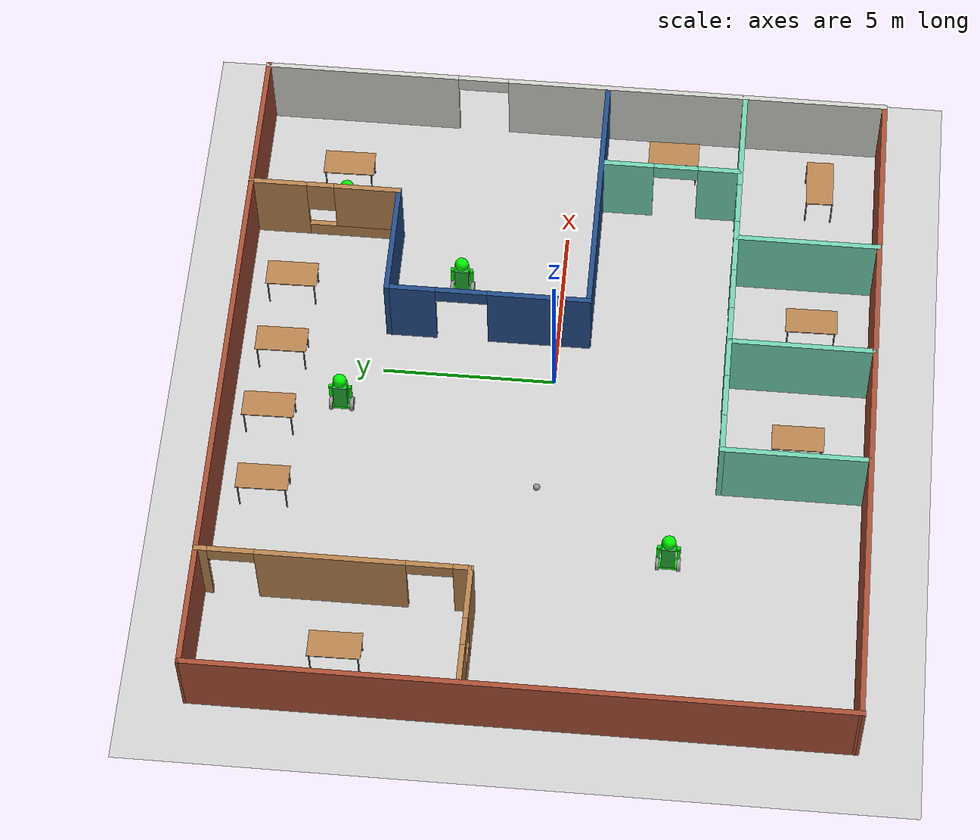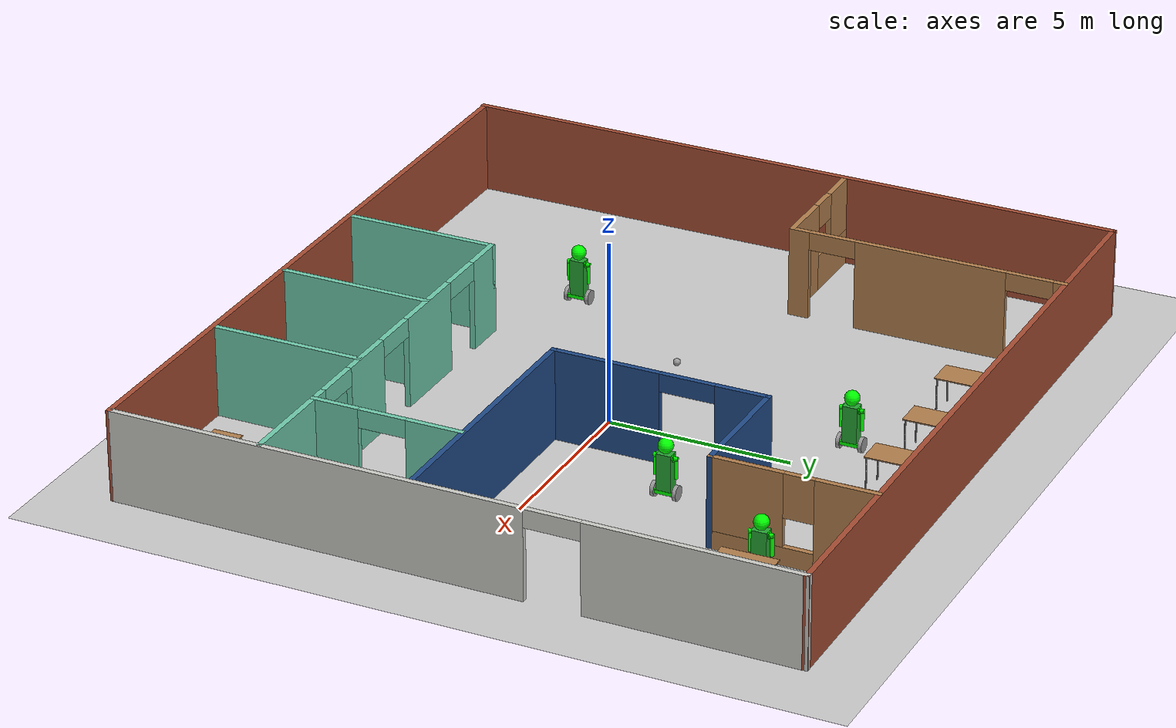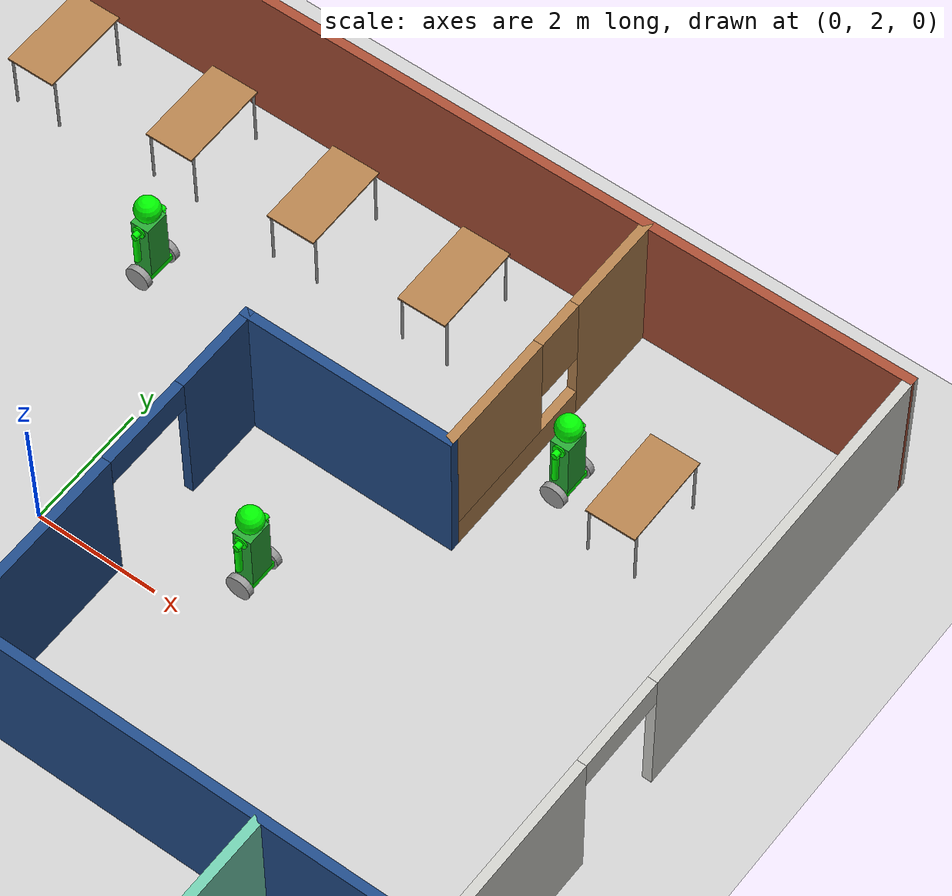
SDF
<sdf version="1.6">
 <world name="default">
  <plugin name="welcome" filename="libwelcome.so"/>
  <light name="sun" type="directional">
   <pose>0 0 10 0 -0 0</pose>
   <diffuse>0.8 0.8 0.8 1</diffuse>
   <specular>0.2 0.2 0.2 1</specular>
   <attenuation>
    <range>1000</range>
    <constant>0.9</constant>
    <linear>0.01</linear>
    <quadratic>0.001</quadratic>
   </attenuation>
   <direction>-0.5 0.1 -0.9</direction>
  </light>
  <model name="ground_plane">
   <static>1</static>
   <link name="link">
    <collision name="collision">
     <geometry><plane><normal>0 0 1</normal><size>100 100</size></plane></geometry>
     <surface>
      <contact><collide_bitmask>65535</collide_bitmask></contact>
      <friction><ode><mu>100</mu><mu2>50</mu2></ode></friction>
     </surface>
    </collision>
    <visual name="visual">
     <cast_shadows>0</cast_shadows>
     <geometry><plane><normal>0 0 1</normal><size>100 100</size></plane></geometry>
     <material>
      <script><uri>file://media/materials/scripts/gazebo.material</uri><name>Gazebo/Grey</name></script>
     </material>
    </visual>
   </link>
  </model>
  <gravity>0 0 -9.8</gravity>
  <magnetic_field>6e-06 2.3e-05 -4.2e-05</magnetic_field>
  <atmosphere type="adiabatic"/>
  <physics name="default_physics" default="0" type="ode">
   <max_step_size>0.001</max_step_size>
   <real_time_factor>1</real_time_factor>
   <real_time_update_rate>1000</real_time_update_rate>
  </physics>
  <scene><ambient>0.4 0.4 0.4 1</ambient><background>0.7 0.7 0.7 1</background><shadows>1</shadows></scene>
  <spherical_coordinates>
   <surface_model>EARTH_WGS84</surface_model>
   <latitude_deg>0</latitude_deg>
   <longitude_deg>0</longitude_deg>
   <elevation>0</elevation>
   <heading_deg>0</heading_deg>
  </spherical_coordinates>
  <model name="office">
   <pose>-1.09853 0.0618 0 0 -0 0</pose>
   <link name="Wall_100">
    <pose>3.87328 -5.05004 0 0 -0 0</pose>
    <visual name="Wall_100_Visual_0">
     <pose>-5.5246 0 1.25 0 -0 0</pose>
     <geometry><box><size>1.2008 0.15 2.5</size></box></geometry>
     <material>
      <script><uri>file://media/materials/scripts/gazebo.material</uri><name>Gazebo/Grey</name></script>
      <ambient>0.435294 0.796078 0.67451 1</ambient>
     </material>
     <meta><layer>0</layer></meta>
    </visual>
    <collision name="Wall_100_Collision_0">
     <geometry><box><size>1.2008 0.15 2.5</size></box></geometry>
     <pose>-5.5246 0 1.25 0 -0 0</pose>
    </collision>
    <visual name="Wall_100_Visual_1">
     <pose>-2.48178 0 1.25 0 -0 0</pose>
     <geometry><box><size>2.28483 0.15 2.5</size></box></geometry>
     <material>
      <script><uri>file://media/materials/scripts/gazebo.material</uri><name>Gazebo/Grey</name></script>
      <ambient>0.435294 0.796078 0.67451 1</ambient>
     </material>
     <meta><layer>0</layer></meta>
    </visual>
    <collision name="Wall_100_Collision_1">
     <geometry><box><size>2.28483 0.15 2.5</size></box></geometry>
     <pose>-2.48178 0 1.25 0 -0 0</pose>
    </collision>
    <visual name="Wall_100_Visual_2">
     <pose>0.798914 0 1.25 0 -0 0</pose>
     <geometry><box><size>1.67657 0.15 2.5</size></box></geometry>
     <material>
      <script><uri>file://media/materials/scripts/gazebo.material</uri><name>Gazebo/Grey</name></script>
      <ambient>0.435294 0.796078 0.67451 1</ambient>
     </material>
     <meta><layer>0</layer></meta>
    </visual>
    <collision name="Wall_100_Collision_2">
     <geometry><box><size>1.67657 0.15 2.5</size></box></geometry>
     <pose>0.798914 0 1.25 0 -0 0</pose>
    </collision>
    <visual name="Wall_100_Visual_3">
     <pose>4.5311 0 1.25 0 -0 0</pose>
     <geometry><box><size>3.1878 0.15 2.5</size></box></geometry>
     <material>
      <script><uri>file://media/materials/scripts/gazebo.material</uri><name>Gazebo/Grey</name></script>
      <ambient>0.435294 0.796078 0.67451 1</ambient>
     </material>
     <meta><layer>0</layer></meta>
    </visual>
    <collision name="Wall_100_Collision_3">
     <geometry><box><size>3.1878 0.15 2.5</size></box></geometry>
     <pose>4.5311 0 1.25 0 -0 0</pose>
    </collision>
    <visual name="Wall_100_Visual_4">
     <pose>-4.2742 0 2.25 0 -0 0</pose>
     <geometry><box><size>1.3 0.15 0.5</size></box></geometry>
     <material>
      <script><uri>file://media/materials/scripts/gazebo.material</uri><name>Gazebo/Grey</name></script>
      <ambient>0.435294 0.796078 0.67451 1</ambient>
     </material>
     <meta><layer>0</layer></meta>
    </visual>
    <collision name="Wall_100_Collision_4">
     <geometry><box><size>1.3 0.15 0.5</size></box></geometry>
     <pose>-4.2742 0 2.25 0 -0 0</pose>
    </collision>
    <visual name="Wall_100_Visual_5">
     <pose>-0.689371 0 2.25 0 -0 0</pose>
     <geometry><box><size>1.3 0.15 0.5</size></box></geometry>
     <material>
      <script><uri>file://media/materials/scripts/gazebo.material</uri><name>Gazebo/Grey</name></script>
      <ambient>0.435294 0.796078 0.67451 1</ambient>
     </material>
     <meta><layer>0</layer></meta>
    </visual>
    <collision name="Wall_100_Collision_5">
     <geometry><box><size>1.3 0.15 0.5</size></box></geometry>
     <pose>-0.689371 0 2.25 0 -0 0</pose>
    </collision>
    <visual name="Wall_100_Visual_6">
     <pose>2.2872 0 2.25 0 -0 0</pose>
     <geometry><box><size>1.3 0.15 0.5</size></box></geometry>
     <material>
      <script><uri>file://media/materials/scripts/gazebo.material</uri><name>Gazebo/Grey</name></script>
      <ambient>0.435294 0.796078 0.67451 1</ambient>
     </material>
     <meta><layer>0</layer></meta>
    </visual>
    <collision name="Wall_100_Collision_6">
     <geometry><box><size>1.3 0.15 0.5</size></box></geometry>
     <pose>2.2872 0 2.25 0 -0 0</pose>
    </collision>
   </link>
   <link name="Wall_102">
    <collision name="Wall_102_Collision">
     <geometry><box><size>20.1151 0.15 2.5</size></box></geometry>
     <pose>0 0 1.25 0 -0 0</pose>
    </collision>
    <visual name="Wall_102_Visual">
     <pose>0 0 1.25 0 -0 0</pose>
     <geometry><box><size>20.1151 0.15 2.5</size></box></geometry>
     <material>
      <script><uri>file://media/materials/scripts/gazebo.material</uri><name>Gazebo/Bricks</name></script>
      <ambient>1 1 1 1</ambient>
     </material>
     <meta><layer>0</layer></meta>
    </visual>
    <pose>0.012485 9.2376 0 0 -0 0.003515</pose>
   </link>
   <link name="Wall_31">
    <collision name="Wall_31_Collision">
     <geometry><box><size>20.1151 0.15 2.5</size></box></geometry>
     <pose>0 0 1.25 0 -0 0</pose>
    </collision>
    <visual name="Wall_31_Visual">
     <pose>0 0 1.25 0 -0 0</pose>
     <geometry><box><size>20.1151 0.15 2.5</size></box></geometry>
     <material>
      <script><uri>file://media/materials/scripts/gazebo.material</uri><name>Gazebo/Bricks</name></script>
      <ambient>1 1 1 1</ambient>
     </material>
     <meta><layer>0</layer></meta>
    </visual>
    <pose>-0.012543 -9.22507 0 0 -0 0.00228</pose>
   </link>
   <link name="Wall_32">
    <pose>9.9825 0.035189 0 0 -0 1.56944</pose>
    <visual name="Wall_32_Visual_0">
     <pose>-3.6506 0 1.25 0 -0 0</pose>
     <geometry><box><size>11.3242 0.15 2.5</size></box></geometry>
     <material>
      <script><uri>file://media/materials/scripts/gazebo.material</uri><name>Gazebo/CeilingTiled</name></script>
      <ambient>1 1 1 1</ambient>
     </material>
     <meta><layer>0</layer></meta>
    </visual>
    <collision name="Wall_32_Collision_0">
     <geometry><box><size>11.3242 0.15 2.5</size></box></geometry>
     <pose>-3.6506 0 1.25 0 -0 0</pose>
    </collision>
    <visual name="Wall_32_Visual_1">
     <pose>6.41211 0 1.25 0 -0 0</pose>
     <geometry><box><size>5.8012 0.15 2.5</size></box></geometry>
     <material>
      <script><uri>file://media/materials/scripts/gazebo.material</uri><name>Gazebo/CeilingTiled</name></script>
      <ambient>1 1 1 1</ambient>
     </material>
     <meta><layer>0</layer></meta>
    </visual>
    <collision name="Wall_32_Collision_1">
     <geometry><box><size>5.8012 0.15 2.5</size></box></geometry>
     <pose>6.41211 0 1.25 0 -0 0</pose>
    </collision>
    <visual name="Wall_32_Visual_2">
     <pose>2.76151 0 2.25 0 -0 0</pose>
     <geometry><box><size>1.5 0.15 0.5</size></box></geometry>
     <material>
      <script><uri>file://media/materials/scripts/gazebo.material</uri><name>Gazebo/CeilingTiled</name></script>
      <ambient>1 1 1 1</ambient>
     </material>
     <meta><layer>0</layer></meta>
    </visual>
    <collision name="Wall_32_Collision_2">
     <geometry><box><size>1.5 0.15 0.5</size></box></geometry>
     <pose>2.76151 0 2.25 0 -0 0</pose>
    </collision>
   </link>
   <link name="Wall_34">
    <pose>5.77997 7.07751 0 0 -0 -1.5708</pose>
    <visual name="Wall_34_Visual_0">
     <pose>-1.39732 0 1.25 0 -0 0</pose>
     <geometry><box><size>1.70536 0.15 2.5</size></box></geometry>
     <material>
      <script><uri>file://media/materials/scripts/gazebo.material</uri><name>Gazebo/Wood</name></script>
      <ambient>0.12549 0.290196 0.529412 1</ambient>
     </material>
     <meta><layer>0</layer></meta>
    </visual>
    <collision name="Wall_34_Collision_0">
     <geometry><box><size>1.70536 0.15 2.5</size></box></geometry>
     <pose>-1.39732 0 1.25 0 -0 0</pose>
    </collision>
    <visual name="Wall_34_Visual_1">
     <pose>0.852681 0 0.25 0 -0 0</pose>
     <geometry><box><size>2.79464 0.15 0.5</size></box></geometry>
     <material>
      <script><uri>file://media/materials/scripts/gazebo.material</uri><name>Gazebo/Wood</name></script>
      <ambient>0.12549 0.290196 0.529412 1</ambient>
     </material>
     <meta><layer>0</layer></meta>
    </visual>
    <collision name="Wall_34_Collision_1">
     <geometry><box><size>2.79464 0.15 0.5</size></box></geometry>
     <pose>0.852681 0 0.25 0 -0 0</pose>
    </collision>
    <visual name="Wall_34_Visual_2">
     <pose>1.25268 0 1.5 0 -0 0</pose>
     <geometry><box><size>1.99464 0.15 2</size></box></geometry>
     <material>
      <script><uri>file://media/materials/scripts/gazebo.material</uri><name>Gazebo/Wood</name></script>
      <ambient>0.12549 0.290196 0.529412 1</ambient>
     </material>
     <meta><layer>0</layer></meta>
    </visual>
    <collision name="Wall_34_Collision_2">
     <geometry><box><size>1.99464 0.15 2</size></box></geometry>
     <pose>1.25268 0 1.5 0 -0 0</pose>
    </collision>
    <visual name="Wall_34_Visual_3">
     <pose>-0.144637 0 1.9 0 -0 0</pose>
     <geometry><box><size>0.8 0.15 1.2</size></box></geometry>
     <material>
      <script><uri>file://media/materials/scripts/gazebo.material</uri><name>Gazebo/Wood</name></script>
      <ambient>0.12549 0.290196 0.529412 1</ambient>
     </material>
     <meta><layer>0</layer></meta>
    </visual>
    <collision name="Wall_34_Collision_3">
     <geometry><box><size>0.8 0.15 1.2</size></box></geometry>
     <pose>-0.144637 0 1.9 0 -0 0</pose>
    </collision>
   </link>
   <link name="Wall_35">
    <collision name="Wall_35_Collision">
     <geometry><box><size>3.5 0.15 2.5</size></box></geometry>
     <pose>0 0 1.25 0 -0 0</pose>
    </collision>
    <visual name="Wall_35_Visual">
     <pose>0 0 1.25 0 -0 0</pose>
     <geometry><box><size>3.5 0.15 2.5</size></box></geometry>
     <material>
      <script><uri>file://media/materials/scripts/gazebo.material</uri><name>Gazebo/Grey</name></script>
      <ambient>0.12549 0.290196 0.529412 1</ambient>
     </material>
     <meta><layer>0</layer></meta>
    </visual>
    <pose>4.10497 4.90251 0 0 -0 3.14159</pose>
   </link>
   <link name="Wall_40">
    <pose>2.42997 1.97751 0 0 -0 -1.5708</pose>
    <visual name="Wall_40_Visual_0">
     <pose>-2.25699 0 1.25 0 -0 0</pose>
     <geometry><box><size>1.48601 0.15 2.5</size></box></geometry>
     <material>
      <script><uri>file://media/materials/scripts/gazebo.material</uri><name>Gazebo/Grey</name></script>
      <ambient>0.12549 0.290196 0.529412 1</ambient>
     </material>
     <meta><layer>0</layer></meta>
    </visual>
    <collision name="Wall_40_Collision_0">
     <geometry><box><size>1.48601 0.15 2.5</size></box></geometry>
     <pose>-2.25699 0 1.25 0 -0 0</pose>
    </collision>
    <visual name="Wall_40_Visual_1">
     <pose>1.493 0 1.25 0 -0 0</pose>
     <geometry><box><size>3.01399 0.15 2.5</size></box></geometry>
     <material>
      <script><uri>file://media/materials/scripts/gazebo.material</uri><name>Gazebo/Grey</name></script>
      <ambient>0.12549 0.290196 0.529412 1</ambient>
     </material>
     <meta><layer>0</layer></meta>
    </visual>
    <collision name="Wall_40_Collision_1">
     <geometry><box><size>3.01399 0.15 2.5</size></box></geometry>
     <pose>1.493 0 1.25 0 -0 0</pose>
    </collision>
    <visual name="Wall_40_Visual_2">
     <pose>-0.76399 0 2.25 0 -0 0</pose>
     <geometry><box><size>1.5 0.15 0.5</size></box></geometry>
     <material>
      <script><uri>file://media/materials/scripts/gazebo.material</uri><name>Gazebo/Grey</name></script>
      <ambient>0.12549 0.290196 0.529412 1</ambient>
     </material>
     <meta><layer>0</layer></meta>
    </visual>
    <collision name="Wall_40_Collision_2">
     <geometry><box><size>1.5 0.15 0.5</size></box></geometry>
     <pose>-0.76399 0 2.25 0 -0 0</pose>
    </collision>
   </link>
   <link name="Wall_43">
    <collision name="Wall_43_Collision">
     <geometry><box><size>18.6254 0.15 2.5</size></box></geometry>
     <pose>0 0 1.25 0 -0 0</pose>
    </collision>
    <visual name="Wall_43_Visual">
     <pose>0 0 1.25 0 -0 0</pose>
     <geometry><box><size>18.6254 0.15 2.5</size></box></geometry>
     <material>
      <script><uri>file://media/materials/scripts/gazebo.material</uri><name>Gazebo/Bricks</name></script>
      <ambient>1 1 1 1</ambient>
     </material>
     <meta><layer>0</layer></meta>
    </visual>
    <pose>-9.98256 -0.035189 0 0 -0 1.56944</pose>
   </link>
   <link name="Wall_58">
    <collision name="Wall_58_Collision">
     <geometry><box><size>7.55 0.15 2.5</size></box></geometry>
     <pose>0 0 1.25 0 -0 0</pose>
    </collision>
    <visual name="Wall_58_Visual">
     <pose>0 0 1.25 0 -0 0</pose>
     <geometry><box><size>7.55 0.15 2.5</size></box></geometry>
     <material>
      <script><uri>file://media/materials/scripts/gazebo.material</uri><name>Gazebo/Grey</name></script>
      <ambient>0.12549 0.290196 0.529412 1</ambient>
     </material>
     <meta><layer>0</layer></meta>
    </visual>
    <pose>6.12997 -0.947492 0 0 -0 0</pose>
   </link>
   <link name="Wall_83">
    <pose>-6.499 5.40169 0 0 -0 -1.5708</pose>
    <visual name="Wall_83_Visual_0">
     <pose>-3.68643 0 1.25 0 -0 0</pose>
     <geometry><box><size>0.377131 0.15 2.5</size></box></geometry>
     <material>
      <script><uri>file://media/materials/scripts/gazebo.material</uri><name>Gazebo/Wood</name></script>
      <ambient>0.996078 0.47451 0.0196078 1</ambient>
     </material>
     <meta><layer>0</layer></meta>
    </visual>
    <collision name="Wall_83_Collision_0">
     <geometry><box><size>0.377131 0.15 2.5</size></box></geometry>
     <pose>-3.68643 0 1.25 0 -0 0</pose>
    </collision>
    <visual name="Wall_83_Visual_1">
     <pose>-0.095603 0 1.25 0 -0 0</pose>
     <geometry><box><size>4.20453 0.15 2.5</size></box></geometry>
     <material>
      <script><uri>file://media/materials/scripts/gazebo.material</uri><name>Gazebo/Wood</name></script>
      <ambient>0.996078 0.47451 0.0196078 1</ambient>
     </material>
     <meta><layer>0</layer></meta>
    </visual>
    <collision name="Wall_83_Collision_1">
     <geometry><box><size>4.20453 0.15 2.5</size></box></geometry>
     <pose>-0.095603 0 1.25 0 -0 0</pose>
    </collision>
    <visual name="Wall_83_Visual_2">
     <pose>3.59083 0 1.25 0 -0 0</pose>
     <geometry><box><size>0.568336 0.15 2.5</size></box></geometry>
     <material>
      <script><uri>file://media/materials/scripts/gazebo.material</uri><name>Gazebo/Wood</name></script>
      <ambient>0.996078 0.47451 0.0196078 1</ambient>
     </material>
     <meta><layer>0</layer></meta>
    </visual>
    <collision name="Wall_83_Collision_2">
     <geometry><box><size>0.568336 0.15 2.5</size></box></geometry>
     <pose>3.59083 0 1.25 0 -0 0</pose>
    </collision>
    <visual name="Wall_83_Visual_3">
     <pose>-2.84787 0 2.25 0 -0 0</pose>
     <geometry><box><size>1.3 0.15 0.5</size></box></geometry>
     <material>
      <script><uri>file://media/materials/scripts/gazebo.material</uri><name>Gazebo/Wood</name></script>
      <ambient>0.996078 0.47451 0.0196078 1</ambient>
     </material>
     <meta><layer>0</layer></meta>
    </visual>
    <collision name="Wall_83_Collision_3">
     <geometry><box><size>1.3 0.15 0.5</size></box></geometry>
     <pose>-2.84787 0 2.25 0 -0 0</pose>
    </collision>
    <visual name="Wall_83_Visual_4">
     <pose>2.65666 0 2.25 0 -0 0</pose>
     <geometry><box><size>1.3 0.15 0.5</size></box></geometry>
     <material>
      <script><uri>file://media/materials/scripts/gazebo.material</uri><name>Gazebo/Wood</name></script>
      <ambient>0.996078 0.47451 0.0196078 1</ambient>
     </material>
     <meta><layer>0</layer></meta>
    </visual>
    <collision name="Wall_83_Collision_4">
     <geometry><box><size>1.3 0.15 0.5</size></box></geometry>
     <pose>2.65666 0 2.25 0 -0 0</pose>
    </collision>
   </link>
   <link name="Wall_84">
    <pose>-8.17411 1.60163 0 0 -0 -3.14156</pose>
    <visual name="Wall_84_Visual_0">
     <pose>-0.938412 0 1.25 0 -0 0</pose>
     <geometry><box><size>1.62318 0.15 2.5</size></box></geometry>
     <material>
      <script><uri>file://media/materials/scripts/gazebo.material</uri><name>Gazebo/Wood</name></script>
      <ambient>0.996078 0.47451 0.0196078 1</ambient>
     </material>
     <meta><layer>0</layer></meta>
    </visual>
    <collision name="Wall_84_Collision_0">
     <geometry><box><size>1.62318 0.15 2.5</size></box></geometry>
     <pose>-0.938412 0 1.25 0 -0 0</pose>
    </collision>
    <visual name="Wall_84_Visual_1">
     <pose>0.811588 0 0.5 0 -0 0</pose>
     <geometry><box><size>1.87682 0.15 1</size></box></geometry>
     <material>
      <script><uri>file://media/materials/scripts/gazebo.material</uri><name>Gazebo/Wood</name></script>
      <ambient>0.996078 0.47451 0.0196078 1</ambient>
     </material>
     <meta><layer>0</layer></meta>
    </visual>
    <collision name="Wall_84_Collision_1">
     <geometry><box><size>1.87682 0.15 1</size></box></geometry>
     <pose>0.811588 0 0.5 0 -0 0</pose>
    </collision>
    <visual name="Wall_84_Visual_2">
     <pose>1.21159 0 1.75 0 -0 0</pose>
     <geometry><box><size>1.07682 0.15 1.5</size></box></geometry>
     <material>
      <script><uri>file://media/materials/scripts/gazebo.material</uri><name>Gazebo/Wood</name></script>
      <ambient>0.996078 0.47451 0.0196078 1</ambient>
     </material>
     <meta><layer>0</layer></meta>
    </visual>
    <collision name="Wall_84_Collision_2">
     <geometry><box><size>1.07682 0.15 1.5</size></box></geometry>
     <pose>1.21159 0 1.75 0 -0 0</pose>
    </collision>
    <visual name="Wall_84_Visual_3">
     <pose>0.273176 0 2.15 0 -0 0</pose>
     <geometry><box><size>0.8 0.15 0.7</size></box></geometry>
     <material>
      <script><uri>file://media/materials/scripts/gazebo.material</uri><name>Gazebo/Wood</name></script>
      <ambient>0.996078 0.47451 0.0196078 1</ambient>
     </material>
     <meta><layer>0</layer></meta>
    </visual>
    <collision name="Wall_84_Collision_3">
     <geometry><box><size>0.8 0.15 0.7</size></box></geometry>
     <pose>0.273176 0 2.15 0 -0 0</pose>
    </collision>
   </link>
   <link name="Wall_87">
    <pose>7.28385 -3.02299 0 0 -0 -1.5708</pose>
    <visual name="Wall_87_Visual_0">
     <pose>-1.31272 0 1.25 0 -0 0</pose>
     <geometry><box><size>1.57456 0.15 2.5</size></box></geometry>
     <material>
      <script><uri>file://media/materials/scripts/gazebo.material</uri><name>Gazebo/Grey</name></script>
      <ambient>0.435294 0.796078 0.67451 1</ambient>
     </material>
     <meta><layer>0</layer></meta>
    </visual>
    <collision name="Wall_87_Collision_0">
     <geometry><box><size>1.57456 0.15 2.5</size></box></geometry>
     <pose>-1.31272 0 1.25 0 -0 0</pose>
    </collision>
    <visual name="Wall_87_Visual_1">
     <pose>1.43728 0 1.25 0 -0 0</pose>
     <geometry><box><size>1.32543 0.15 2.5</size></box></geometry>
     <material>
      <script><uri>file://media/materials/scripts/gazebo.material</uri><name>Gazebo/Grey</name></script>
      <ambient>0.435294 0.796078 0.67451 1</ambient>
     </material>
     <meta><layer>0</layer></meta>
    </visual>
    <collision name="Wall_87_Collision_1">
     <geometry><box><size>1.32543 0.15 2.5</size></box></geometry>
     <pose>1.43728 0 1.25 0 -0 0</pose>
    </collision>
    <visual name="Wall_87_Visual_2">
     <pose>0.124565 0 2.25 0 -0 0</pose>
     <geometry><box><size>1.3 0.15 0.5</size></box></geometry>
     <material>
      <script><uri>file://media/materials/scripts/gazebo.material</uri><name>Gazebo/Grey</name></script>
      <ambient>0.435294 0.796078 0.67451 1</ambient>
     </material>
     <meta><layer>0</layer></meta>
    </visual>
    <collision name="Wall_87_Collision_2">
     <geometry><box><size>1.3 0.15 0.5</size></box></geometry>
     <pose>0.124565 0 2.25 0 -0 0</pose>
    </collision>
   </link>
   <link name="Wall_89">
    <collision name="Wall_89_Collision">
     <geometry><box><size>4.25 0.15 2.5</size></box></geometry>
     <pose>0 0 1.25 0 -0 0</pose>
    </collision>
    <visual name="Wall_89_Visual">
     <pose>0 0 1.25 0 -0 0</pose>
     <geometry><box><size>4.25 0.15 2.5</size></box></geometry>
     <material>
      <script><uri>file://media/materials/scripts/gazebo.material</uri><name>Gazebo/Grey</name></script>
      <ambient>0.435294 0.796078 0.67451 1</ambient>
     </material>
     <meta><layer>0</layer></meta>
    </visual>
    <pose>4.96424 -7.13054 0 0 -0 -1.5708</pose>
   </link>
   <link name="Wall_91">
    <collision name="Wall_91_Collision">
     <geometry><box><size>4.25 0.15 2.5</size></box></geometry>
     <pose>0 0 1.25 0 -0 0</pose>
    </collision>
    <visual name="Wall_91_Visual">
     <pose>0 0 1.25 0 -0 0</pose>
     <geometry><box><size>4.25 0.15 2.5</size></box></geometry>
     <material>
      <script><uri>file://media/materials/scripts/gazebo.material</uri><name>Gazebo/Grey</name></script>
      <ambient>0.435294 0.796078 0.67451 1</ambient>
     </material>
     <meta><layer>0</layer></meta>
    </visual>
    <pose>1.40966 -7.1075 0 0 -0 -1.5708</pose>
   </link>
   <link name="Wall_93">
    <collision name="Wall_93_Collision">
     <geometry><box><size>4.25 0.15 2.5</size></box></geometry>
     <pose>0 0 1.25 0 -0 0</pose>
    </collision>
    <visual name="Wall_93_Visual">
     <pose>0 0 1.25 0 -0 0</pose>
     <geometry><box><size>4.25 0.15 2.5</size></box></geometry>
     <material>
      <script><uri>file://media/materials/scripts/gazebo.material</uri><name>Gazebo/Grey</name></script>
      <ambient>0.435294 0.796078 0.67451 1</ambient>
     </material>
     <meta><layer>0</layer></meta>
    </visual>
    <pose>-2.17672 -7.10004 0 0 -0 -1.5708</pose>
   </link>
   <static>1</static>
  </model>
  <model name="humanoid_robot">
   <link name="link_0">
    <pose>0 0 -0.1375 0 -0 0</pose>
    <inertial>
     <mass>10</mass>
     <inertia>
      <ixx>0.216667</ixx>
      <ixy>0</ixy>
      <ixz>0</ixz>
      <iyy>0.0833333</iyy>
      <iyz>0</iyz>
      <izz>0.283333</izz>
     </inertia>
    </inertial>
    <visual name="visual">
     <geometry><box><size>0.3 0.5 0.1</size></box></geometry>
     <material>
      <lighting>1</lighting>
      <script><uri>file://media/materials/scripts/gazebo.material</uri><name>Gazebo/Grey</name></script>
      <shader type="pixel"><normal_map>__default__</normal_map></shader>
      <ambient>0 1 0 1</ambient>
      <diffuse>0.7 0.7 0.7 1</diffuse>
      <specular>0.01 0.01 0.01 1</specular>
      <emissive>0 0 0 1</emissive>
     </material>
    </visual>
    <collision name="collision">
     <geometry><box><size>0.3 0.5 0.1</size></box></geometry>
     <surface>
      <friction>
       <ode><mu>1</mu><mu2>1</mu2><fdir1>0 0 0</fdir1><slip1>0</slip1><slip2>0</slip2></ode>
       <torsional>
        <coefficient>1</coefficient>
        <patch_radius>0</patch_radius>
        <surface_radius>0</surface_radius>
        <use_patch_radius>1</use_patch_radius>
        <ode><slip>0</slip></ode>
       </torsional>
      </friction>
      <bounce><restitution_coefficient>0</restitution_coefficient><threshold>1e+06</threshold></bounce>
      <contact>
       <collide_without_contact>0</collide_without_contact>
       <collide_without_contact_bitmask>1</collide_without_contact_bitmask>
       <collide_bitmask>1</collide_bitmask>
       <ode>
        <soft_cfm>0</soft_cfm>
        <soft_erp>0.2</soft_erp>
        <kp>1e+13</kp>
        <kd>1</kd>
        <max_vel>0.01</max_vel>
        <min_depth>0</min_depth>
       </ode>
       <bullet>
        <split_impulse>1</split_impulse>
        <split_impulse_penetration_threshold>-0.01</split_impulse_penetration_threshold>
        <soft_cfm>0</soft_cfm>
        <soft_erp>0.2</soft_erp>
        <kp>1e+13</kp>
        <kd>1</kd>
       </bullet>
      </contact>
     </surface>
    </collision>
   </link>
   <link name="link_0_0">
    <pose>0 0 1.1125 0 -0 0</pose>
    <inertial>
     <mass>0.25</mass>
     <inertia><ixx>0.1</ixx><ixy>0</ixy><ixz>0</ixz><iyy>0.1</iyy><iyz>0</iyz><izz>0.1</izz></inertia>
    </inertial>
    <visual name="visual">
     <geometry><sphere><radius>0.2</radius></sphere></geometry>
     <material>
      <lighting>1</lighting>
      <script><uri>file://media/materials/scripts/gazebo.material</uri><name>Gazebo/Grey</name></script>
      <shader type="pixel"><normal_map>__default__</normal_map></shader>
      <ambient>0 1 0 1</ambient>
      <diffuse>0.7 0.7 0.7 1</diffuse>
      <specular>0.01 0.01 0.01 1</specular>
      <emissive>0 0 0 1</emissive>
     </material>
    </visual>
    <collision name="collision">
     <geometry><sphere><radius>0.2</radius></sphere></geometry>
     <surface>
      <friction>
       <ode><mu>1</mu><mu2>1</mu2><fdir1>0 0 0</fdir1><slip1>0</slip1><slip2>0</slip2></ode>
       <torsional>
        <coefficient>1</coefficient>
        <patch_radius>0</patch_radius>
        <surface_radius>0</surface_radius>
        <use_patch_radius>1</use_patch_radius>
        <ode><slip>0</slip></ode>
       </torsional>
      </friction>
      <bounce><restitution_coefficient>0</restitution_coefficient><threshold>1e+06</threshold></bounce>
      <contact>
       <collide_without_contact>0</collide_without_contact>
       <collide_without_contact_bitmask>1</collide_without_contact_bitmask>
       <collide_bitmask>1</collide_bitmask>
       <ode>
        <soft_cfm>0</soft_cfm>
        <soft_erp>0.2</soft_erp>
        <kp>1e+13</kp>
        <kd>1</kd>
        <max_vel>0.01</max_vel>
        <min_depth>0</min_depth>
       </ode>
       <bullet>
        <split_impulse>1</split_impulse>
        <split_impulse_penetration_threshold>-0.01</split_impulse_penetration_threshold>
        <soft_cfm>0</soft_cfm>
        <soft_erp>0.2</soft_erp>
        <kp>1e+13</kp>
        <kd>1</kd>
       </bullet>
      </contact>
     </surface>
    </collision>
   </link>
   <link name="link_1">
    <pose>0 -0.300019 -0.137182 1.5707 -0 0</pose>
    <inertial>
     <mass>1</mass>
     <inertia><ixx>0.145833</ixx><ixy>0</ixy><ixz>0</ixz><iyy>0.145833</iyy><iyz>0</iyz><izz>0.125</izz></inertia>
    </inertial>
    <visual name="visual">
     <geometry><cylinder><radius>0.2</radius><length>0.1</length></cylinder></geometry>
     <material>
      <lighting>1</lighting>
      <script><uri>file://media/materials/scripts/gazebo.material</uri><name>Gazebo/Grey</name></script>
      <shader type="pixel"><normal_map>__default__</normal_map></shader>
      <ambient>1 1 1 1</ambient>
      <diffuse>0.7 0.7 0.7 1</diffuse>
      <specular>0.01 0.01 0.01 1</specular>
      <emissive>0 0 0 1</emissive>
     </material>
    </visual>
    <collision name="collision">
     <geometry><cylinder><radius>0.2</radius><length>0.1</length></cylinder></geometry>
     <surface>
      <friction>
       <ode><mu>1</mu><mu2>1</mu2><fdir1>0 0 0</fdir1><slip1>0</slip1><slip2>0</slip2></ode>
       <torsional>
        <coefficient>1</coefficient>
        <patch_radius>0</patch_radius>
        <surface_radius>0</surface_radius>
        <use_patch_radius>1</use_patch_radius>
        <ode><slip>0</slip></ode>
       </torsional>
      </friction>
      <bounce><restitution_coefficient>0</restitution_coefficient><threshold>1e+06</threshold></bounce>
      <contact>
       <collide_without_contact>0</collide_without_contact>
       <collide_without_contact_bitmask>1</collide_without_contact_bitmask>
       <collide_bitmask>1</collide_bitmask>
       <ode>
        <soft_cfm>0</soft_cfm>
        <soft_erp>0.2</soft_erp>
        <kp>1e+13</kp>
        <kd>1</kd>
        <max_vel>0.01</max_vel>
        <min_depth>0</min_depth>
       </ode>
       <bullet>
        <split_impulse>1</split_impulse>
        <split_impulse_penetration_threshold>-0.01</split_impulse_penetration_threshold>
        <soft_cfm>0</soft_cfm>
        <soft_erp>0.2</soft_erp>
        <kp>1e+13</kp>
        <kd>1</kd>
       </bullet>
      </contact>
     </surface>
    </collision>
   </link>
   <link name="link_1_0">
    <pose>0 -0.275033 0.812507 1.5707 -0 0</pose>
    <inertial>
     <mass>0.1</mass>
     <inertia><ixx>0.145833</ixx><ixy>0</ixy><ixz>0</ixz><iyy>0.145833</iyy><iyz>0</iyz><izz>0.125</izz></inertia>
    </inertial>
    <visual name="visual">
     <geometry><cylinder><radius>0.05</radius><length>0.1</length></cylinder></geometry>
     <material>
      <lighting>1</lighting>
      <script><uri>file://media/materials/scripts/gazebo.material</uri><name>Gazebo/Grey</name></script>
      <shader type="pixel"><normal_map>__default__</normal_map></shader>
      <ambient>0 1 0 1</ambient>
      <diffuse>0.7 0.7 0.7 1</diffuse>
      <specular>0.01 0.01 0.01 1</specular>
      <emissive>0 0 0 1</emissive>
     </material>
    </visual>
    <collision name="collision">
     <geometry><cylinder><radius>0.05</radius><length>0.1</length></cylinder></geometry>
     <surface>
      <friction>
       <ode><mu>1</mu><mu2>1</mu2><fdir1>0 0 0</fdir1><slip1>0</slip1><slip2>0</slip2></ode>
       <torsional>
        <coefficient>1</coefficient>
        <patch_radius>0</patch_radius>
        <surface_radius>0</surface_radius>
        <use_patch_radius>1</use_patch_radius>
        <ode><slip>0</slip></ode>
       </torsional>
      </friction>
      <bounce><restitution_coefficient>0</restitution_coefficient><threshold>1e+06</threshold></bounce>
      <contact>
       <collide_without_contact>0</collide_without_contact>
       <collide_without_contact_bitmask>1</collide_without_contact_bitmask>
       <collide_bitmask>1</collide_bitmask>
       <ode>
        <soft_cfm>0</soft_cfm>
        <soft_erp>0.2</soft_erp>
        <kp>1e+13</kp>
        <kd>1</kd>
        <max_vel>0.01</max_vel>
        <min_depth>0</min_depth>
       </ode>
       <bullet>
        <split_impulse>1</split_impulse>
        <split_impulse_penetration_threshold>-0.01</split_impulse_penetration_threshold>
        <soft_cfm>0</soft_cfm>
        <soft_erp>0.2</soft_erp>
        <kp>1e+13</kp>
        <kd>1</kd>
       </bullet>
      </contact>
     </surface>
    </collision>
   </link>
   <link name="link_1_0_clone">
    <pose>0 0.275024 0.812479 1.5707 -0 0</pose>
    <inertial>
     <mass>0.1</mass>
     <inertia><ixx>0.145833</ixx><ixy>0</ixy><ixz>0</ixz><iyy>0.145833</iyy><iyz>0</iyz><izz>0.125</izz></inertia>
    </inertial>
    <visual name="visual_0">
     <geometry><cylinder><radius>0.05</radius><length>0.1</length></cylinder></geometry>
     <material>
      <lighting>1</lighting>
      <script><uri>file://media/materials/scripts/gazebo.material</uri><name>Gazebo/Grey</name></script>
      <shader type="pixel"><normal_map>__default__</normal_map></shader>
      <ambient>0 1 0 1</ambient>
      <diffuse>0.7 0.7 0.7 1</diffuse>
      <specular>0.01 0.01 0.01 1</specular>
      <emissive>0 0 0 1</emissive>
     </material>
    </visual>
    <collision name="collision">
     <geometry><cylinder><radius>0.05</radius><length>0.1</length></cylinder></geometry>
     <surface>
      <friction>
       <ode><mu>1</mu><mu2>1</mu2><fdir1>0 0 0</fdir1><slip1>0</slip1><slip2>0</slip2></ode>
       <torsional>
        <coefficient>1</coefficient>
        <patch_radius>0</patch_radius>
        <surface_radius>0</surface_radius>
        <use_patch_radius>1</use_patch_radius>
        <ode><slip>0</slip></ode>
       </torsional>
      </friction>
      <bounce><restitution_coefficient>0</restitution_coefficient><threshold>1e+06</threshold></bounce>
      <contact>
       <collide_without_contact>0</collide_without_contact>
       <collide_without_contact_bitmask>1</collide_without_contact_bitmask>
       <collide_bitmask>1</collide_bitmask>
       <ode>
        <soft_cfm>0</soft_cfm>
        <soft_erp>0.2</soft_erp>
        <kp>1e+13</kp>
        <kd>1</kd>
        <max_vel>0.01</max_vel>
        <min_depth>0</min_depth>
       </ode>
       <bullet>
        <split_impulse>1</split_impulse>
        <split_impulse_penetration_threshold>-0.01</split_impulse_penetration_threshold>
        <soft_cfm>0</soft_cfm>
        <soft_erp>0.2</soft_erp>
        <kp>1e+13</kp>
        <kd>1</kd>
       </bullet>
      </contact>
     </surface>
    </collision>
   </link>
   <link name="link_1_clone">
    <pose>0 0.300019 -0.137182 1.5707 -0 0</pose>
    <inertial>
     <mass>1</mass>
     <inertia><ixx>0.145833</ixx><ixy>0</ixy><ixz>0</ixz><iyy>0.145833</iyy><iyz>0</iyz><izz>0.125</izz></inertia>
    </inertial>
    <visual name="visual">
     <geometry><cylinder><radius>0.2</radius><length>0.1</length></cylinder></geometry>
     <material>
      <lighting>1</lighting>
      <script><uri>file://media/materials/scripts/gazebo.material</uri><name>Gazebo/Grey</name></script>
      <shader type="pixel"><normal_map>__default__</normal_map></shader>
      <ambient>1 1 1 1</ambient>
      <diffuse>0.7 0.7 0.7 1</diffuse>
      <specular>0.01 0.01 0.01 1</specular>
      <emissive>0 0 0 1</emissive>
     </material>
    </visual>
    <collision name="collision">
     <geometry><cylinder><radius>0.2</radius><length>0.1</length></cylinder></geometry>
     <surface>
      <friction>
       <ode><mu>1</mu><mu2>1</mu2><fdir1>0 0 0</fdir1><slip1>0</slip1><slip2>0</slip2></ode>
       <torsional>
        <coefficient>1</coefficient>
        <patch_radius>0</patch_radius>
        <surface_radius>0</surface_radius>
        <use_patch_radius>1</use_patch_radius>
        <ode><slip>0</slip></ode>
       </torsional>
      </friction>
      <bounce><restitution_coefficient>0</restitution_coefficient><threshold>1e+06</threshold></bounce>
      <contact>
       <collide_without_contact>0</collide_without_contact>
       <collide_without_contact_bitmask>1</collide_without_contact_bitmask>
       <collide_bitmask>1</collide_bitmask>
       <ode>
        <soft_cfm>0</soft_cfm>
        <soft_erp>0.2</soft_erp>
        <kp>1e+13</kp>
        <kd>1</kd>
        <max_vel>0.01</max_vel>
        <min_depth>0</min_depth>
       </ode>
       <bullet>
        <split_impulse>1</split_impulse>
        <split_impulse_penetration_threshold>-0.01</split_impulse_penetration_threshold>
        <soft_cfm>0</soft_cfm>
        <soft_erp>0.2</soft_erp>
        <kp>1e+13</kp>
        <kd>1</kd>
       </bullet>
      </contact>
     </surface>
    </collision>
   </link>
   <link name="link_1_clone_0">
    <pose>0 -0.21251 0.812499 1.5707 -0 0</pose>
    <inertial>
     <mass>1</mass>
     <inertia><ixx>0.145833</ixx><ixy>0</ixy><ixz>0</ixz><iyy>0.145833</iyy><iyz>0</iyz><izz>0.125</izz></inertia>
    </inertial>
    <visual name="visual">
     <geometry><cylinder><radius>0.1</radius><length>0.025</length></cylinder></geometry>
     <material>
      <lighting>1</lighting>
      <script><uri>file://media/materials/scripts/gazebo.material</uri><name>Gazebo/Grey</name></script>
      <shader type="pixel"><normal_map>__default__</normal_map></shader>
      <ambient>0 1 0 1</ambient>
      <diffuse>0.7 0.7 0.7 1</diffuse>
      <specular>0.01 0.01 0.01 1</specular>
      <emissive>0 0 0 1</emissive>
     </material>
    </visual>
    <collision name="collision">
     <geometry><cylinder><radius>0.1</radius><length>0.025</length></cylinder></geometry>
     <surface>
      <friction>
       <ode><mu>1</mu><mu2>1</mu2><fdir1>0 0 0</fdir1><slip1>0</slip1><slip2>0</slip2></ode>
       <torsional>
        <coefficient>1</coefficient>
        <patch_radius>0</patch_radius>
        <surface_radius>0</surface_radius>
        <use_patch_radius>1</use_patch_radius>
        <ode><slip>0</slip></ode>
       </torsional>
      </friction>
      <bounce><restitution_coefficient>0</restitution_coefficient><threshold>1e+06</threshold></bounce>
      <contact>
       <collide_without_contact>0</collide_without_contact>
       <collide_without_contact_bitmask>1</collide_without_contact_bitmask>
       <collide_bitmask>1</collide_bitmask>
       <ode>
        <soft_cfm>0</soft_cfm>
        <soft_erp>0.2</soft_erp>
        <kp>1e+13</kp>
        <kd>1</kd>
        <max_vel>0.01</max_vel>
        <min_depth>0</min_depth>
       </ode>
       <bullet>
        <split_impulse>1</split_impulse>
        <split_impulse_penetration_threshold>-0.01</split_impulse_penetration_threshold>
        <soft_cfm>0</soft_cfm>
        <soft_erp>0.2</soft_erp>
        <kp>1e+13</kp>
        <kd>1</kd>
       </bullet>
      </contact>
     </surface>
    </collision>
   </link>
   <link name="link_1_clone_0_clone">
    <pose>0 0.21251 0.812499 1.5707 -0 0</pose>
    <inertial>
     <mass>1</mass>
     <inertia><ixx>0.145833</ixx><ixy>0</ixy><ixz>0</ixz><iyy>0.145833</iyy><iyz>0</iyz><izz>0.125</izz></inertia>
    </inertial>
    <visual name="visual">
     <geometry><cylinder><radius>0.1</radius><length>0.025</length></cylinder></geometry>
     <material>
      <lighting>1</lighting>
      <script><uri>file://media/materials/scripts/gazebo.material</uri><name>Gazebo/Grey</name></script>
      <shader type="pixel"><normal_map>__default__</normal_map></shader>
      <ambient>0 1 0 1</ambient>
      <diffuse>0.7 0.7 0.7 1</diffuse>
      <specular>0.01 0.01 0.01 1</specular>
      <emissive>0 0 0 1</emissive>
     </material>
    </visual>
    <collision name="collision">
     <geometry><cylinder><radius>0.1</radius><length>0.025</length></cylinder></geometry>
     <surface>
      <friction>
       <ode><mu>1</mu><mu2>1</mu2><fdir1>0 0 0</fdir1><slip1>0</slip1><slip2>0</slip2></ode>
       <torsional>
        <coefficient>1</coefficient>
        <patch_radius>0</patch_radius>
        <surface_radius>0</surface_radius>
        <use_patch_radius>1</use_patch_radius>
        <ode><slip>0</slip></ode>
       </torsional>
      </friction>
      <bounce><restitution_coefficient>0</restitution_coefficient><threshold>1e+06</threshold></bounce>
      <contact>
       <collide_without_contact>0</collide_without_contact>
       <collide_without_contact_bitmask>1</collide_without_contact_bitmask>
       <collide_bitmask>1</collide_bitmask>
       <ode>
        <soft_cfm>0</soft_cfm>
        <soft_erp>0.2</soft_erp>
        <kp>1e+13</kp>
        <kd>1</kd>
        <max_vel>0.01</max_vel>
        <min_depth>0</min_depth>
       </ode>
       <bullet>
        <split_impulse>1</split_impulse>
        <split_impulse_penetration_threshold>-0.01</split_impulse_penetration_threshold>
        <soft_cfm>0</soft_cfm>
        <soft_erp>0.2</soft_erp>
        <kp>1e+13</kp>
        <kd>1</kd>
       </bullet>
      </contact>
     </surface>
    </collision>
   </link>
   <link name="link_3">
    <pose>0 0 0.4125 0 -0 0</pose>
    <inertial>
     <mass>1</mass>
     <inertia>
      <ixx>0.166667</ixx>
      <ixy>0</ixy>
      <ixz>0</ixz>
      <iyy>0.166667</iyy>
      <iyz>0</iyz>
      <izz>0.166667</izz>
     </inertia>
    </inertial>
    <visual name="visual">
     <geometry><box><size>0.3 0.4 1</size></box></geometry>
     <material>
      <lighting>1</lighting>
      <script><uri>file://media/materials/scripts/gazebo.material</uri><name>Gazebo/Green</name></script>
      <shader type="pixel"><normal_map>__default__</normal_map></shader>
      <ambient>0 1 0 1</ambient>
      <diffuse>0.7 0.7 0.7 1</diffuse>
      <specular>0.01 0.01 0.01 1</specular>
      <emissive>0 0 0 1</emissive>
     </material>
    </visual>
    <collision name="collision">
     <geometry><box><size>0.3 0.4 1</size></box></geometry>
     <surface>
      <friction>
       <ode><mu>1</mu><mu2>1</mu2><fdir1>0 0 0</fdir1><slip1>0</slip1><slip2>0</slip2></ode>
       <torsional>
        <coefficient>1</coefficient>
        <patch_radius>0</patch_radius>
        <surface_radius>0</surface_radius>
        <use_patch_radius>1</use_patch_radius>
        <ode><slip>0</slip></ode>
       </torsional>
      </friction>
      <bounce><restitution_coefficient>0</restitution_coefficient><threshold>1e+06</threshold></bounce>
      <contact>
       <collide_without_contact>0</collide_without_contact>
       <collide_without_contact_bitmask>1</collide_without_contact_bitmask>
       <collide_bitmask>1</collide_bitmask>
       <ode>
        <soft_cfm>0</soft_cfm>
        <soft_erp>0.2</soft_erp>
        <kp>1e+13</kp>
        <kd>1</kd>
        <max_vel>0.01</max_vel>
        <min_depth>0</min_depth>
       </ode>
       <bullet>
        <split_impulse>1</split_impulse>
        <split_impulse_penetration_threshold>-0.01</split_impulse_penetration_threshold>
        <soft_cfm>0</soft_cfm>
        <soft_erp>0.2</soft_erp>
        <kp>1e+13</kp>
        <kd>1</kd>
       </bullet>
      </contact>
     </surface>
    </collision>
   </link>
   <link name="link_3_0">
    <pose>0 -0.285062 0.512562 0 -0 0</pose>
    <inertial>
     <mass>0.5</mass>
     <inertia><ixx>0.145833</ixx><ixy>0</ixy><ixz>0</ixz><iyy>0.145833</iyy><iyz>0</iyz><izz>0.125</izz></inertia>
    </inertial>
    <visual name="visual">
     <geometry><cylinder><radius>0.05</radius><length>0.5</length></cylinder></geometry>
     <material>
      <lighting>1</lighting>
      <script><uri>file://media/materials/scripts/gazebo.material</uri><name>Gazebo/Grey</name></script>
      <shader type="pixel"><normal_map>__default__</normal_map></shader>
      <ambient>0 1 0 1</ambient>
      <diffuse>0.7 0.7 0.7 1</diffuse>
      <specular>0.01 0.01 0.01 1</specular>
      <emissive>0 0 0 1</emissive>
     </material>
    </visual>
    <collision name="collision">
     <geometry><cylinder><radius>0.05</radius><length>0.5</length></cylinder></geometry>
     <surface>
      <friction>
       <ode><mu>1</mu><mu2>1</mu2><fdir1>0 0 0</fdir1><slip1>0</slip1><slip2>0</slip2></ode>
       <torsional>
        <coefficient>1</coefficient>
        <patch_radius>0</patch_radius>
        <surface_radius>0</surface_radius>
        <use_patch_radius>1</use_patch_radius>
        <ode><slip>0</slip></ode>
       </torsional>
      </friction>
      <bounce><restitution_coefficient>0</restitution_coefficient><threshold>1e+06</threshold></bounce>
      <contact>
       <collide_without_contact>0</collide_without_contact>
       <collide_without_contact_bitmask>1</collide_without_contact_bitmask>
       <collide_bitmask>1</collide_bitmask>
       <ode>
        <soft_cfm>0</soft_cfm>
        <soft_erp>0.2</soft_erp>
        <kp>1e+13</kp>
        <kd>1</kd>
        <max_vel>0.01</max_vel>
        <min_depth>0</min_depth>
       </ode>
       <bullet>
        <split_impulse>1</split_impulse>
        <split_impulse_penetration_threshold>-0.01</split_impulse_penetration_threshold>
        <soft_cfm>0</soft_cfm>
        <soft_erp>0.2</soft_erp>
        <kp>1e+13</kp>
        <kd>1</kd>
       </bullet>
      </contact>
     </surface>
    </collision>
   </link>
   <link name="link_3_0_clone">
    <pose>0 0.284995 0.512478 0 -0 0</pose>
    <inertial>
     <mass>0.5</mass>
     <inertia><ixx>0.145833</ixx><ixy>0</ixy><ixz>0</ixz><iyy>0.145833</iyy><iyz>0</iyz><izz>0.125</izz></inertia>
    </inertial>
    <visual name="visual_0">
     <geometry><cylinder><radius>0.05</radius><length>0.5</length></cylinder></geometry>
     <material>
      <lighting>1</lighting>
      <script><uri>file://media/materials/scripts/gazebo.material</uri><name>Gazebo/Grey</name></script>
      <shader type="pixel"><normal_map>__default__</normal_map></shader>
      <ambient>0 1 0 1</ambient>
      <diffuse>0.7 0.7 0.7 1</diffuse>
      <specular>0.01 0.01 0.01 1</specular>
      <emissive>0 0 0 1</emissive>
     </material>
    </visual>
    <collision name="collision">
     <geometry><cylinder><radius>0.05</radius><length>0.5</length></cylinder></geometry>
     <surface>
      <friction>
       <ode><mu>1</mu><mu2>1</mu2><fdir1>0 0 0</fdir1><slip1>0</slip1><slip2>0</slip2></ode>
       <torsional>
        <coefficient>1</coefficient>
        <patch_radius>0</patch_radius>
        <surface_radius>0</surface_radius>
        <use_patch_radius>1</use_patch_radius>
        <ode><slip>0</slip></ode>
       </torsional>
      </friction>
      <bounce><restitution_coefficient>0</restitution_coefficient><threshold>1e+06</threshold></bounce>
      <contact>
       <collide_without_contact>0</collide_without_contact>
       <collide_without_contact_bitmask>1</collide_without_contact_bitmask>
       <collide_bitmask>1</collide_bitmask>
       <ode>
        <soft_cfm>0</soft_cfm>
        <soft_erp>0.2</soft_erp>
        <kp>1e+13</kp>
        <kd>1</kd>
        <max_vel>0.01</max_vel>
        <min_depth>0</min_depth>
       </ode>
       <bullet>
        <split_impulse>1</split_impulse>
        <split_impulse_penetration_threshold>-0.01</split_impulse_penetration_threshold>
        <soft_cfm>0</soft_cfm>
        <soft_erp>0.2</soft_erp>
        <kp>1e+13</kp>
        <kd>1</kd>
       </bullet>
      </contact>
     </surface>
    </collision>
   </link>
   <joint name="link_0_JOINT_2" type="fixed">
    <parent>link_0</parent>
    <child>link_3</child>
    <physics>
     <ode><limit><cfm>0</cfm><erp>0.2</erp></limit><suspension><cfm>0</cfm><erp>0.2</erp></suspension></ode>
    </physics>
   </joint>
   <joint name="link_0_JOINT_3" type="revolute">
    <parent>link_0</parent>
    <child>link_1</child>
    <axis>
     <xyz>0 0 -1</xyz>
     <use_parent_model_frame>0</use_parent_model_frame>
     <limit>
      <lower>-1.79769e+308</lower>
      <upper>1.79769e+308</upper>
      <effort>-1</effort>
      <velocity>-1</velocity>
     </limit>
     <dynamics>
      <spring_reference>0</spring_reference>
      <spring_stiffness>0</spring_stiffness>
      <damping>0</damping>
     </dynamics>
    </axis>
    <physics>
     <ode><limit><cfm>0</cfm><erp>0.2</erp></limit><suspension><cfm>0</cfm><erp>0.2</erp></suspension></ode>
    </physics>
   </joint>
   <joint name="link_0_JOINT_5" type="revolute">
    <parent>link_0</parent>
    <child>link_1_clone</child>
    <axis>
     <xyz>0 0 1</xyz>
     <use_parent_model_frame>0</use_parent_model_frame>
     <limit>
      <lower>-1.79769e+308</lower>
      <upper>1.79769e+308</upper>
      <effort>-1</effort>
      <velocity>-1</velocity>
     </limit>
     <dynamics>
      <spring_reference>0</spring_reference>
      <spring_stiffness>0</spring_stiffness>
      <damping>0</damping>
     </dynamics>
    </axis>
    <physics>
     <ode><limit><cfm>0</cfm><erp>0.2</erp></limit><suspension><cfm>0</cfm><erp>0.2</erp></suspension></ode>
    </physics>
   </joint>
   <joint name="link_1_0_JOINT_16" type="fixed">
    <parent>link_1_0</parent>
    <child>link_3_0</child>
    <physics>
     <ode><limit><cfm>0</cfm><erp>0.2</erp></limit><suspension><cfm>0</cfm><erp>0.2</erp></suspension></ode>
    </physics>
   </joint>
   <joint name="link_1_0_clone_JOINT_17" type="fixed">
    <parent>link_1_0_clone</parent>
    <child>link_3_0_clone</child>
    <physics>
     <ode><limit><cfm>0</cfm><erp>0.2</erp></limit><suspension><cfm>0</cfm><erp>0.2</erp></suspension></ode>
    </physics>
   </joint>
   <joint name="link_1_clone_0_JOINT_10" type="revolute">
    <parent>link_1_clone_0</parent>
    <child>link_1_0</child>
    <axis>
     <xyz>0 0 1</xyz>
     <use_parent_model_frame>0</use_parent_model_frame>
     <limit>
      <lower>-1.79769e+308</lower>
      <upper>1.79769e+308</upper>
      <effort>50</effort>
      <velocity>-1</velocity>
     </limit>
     <dynamics>
      <spring_reference>0</spring_reference>
      <spring_stiffness>0</spring_stiffness>
      <damping>0</damping>
      <friction>0</friction>
     </dynamics>
    </axis>
    <physics>
     <ode><limit><cfm>0</cfm><erp>0.2</erp></limit><suspension><cfm>0</cfm><erp>0.2</erp></suspension></ode>
    </physics>
   </joint>
   <joint name="link_1_clone_0_clone_JOINT_0" type="revolute">
    <parent>link_1_clone_0_clone</parent>
    <child>link_1_0_clone</child>
    <axis>
     <xyz>0 0 1</xyz>
     <use_parent_model_frame>0</use_parent_model_frame>
     <limit>
      <lower>-1.79769e+308</lower>
      <upper>1.79769e+308</upper>
      <effort>50</effort>
      <velocity>-1</velocity>
     </limit>
     <dynamics>
      <spring_reference>0</spring_reference>
      <spring_stiffness>0</spring_stiffness>
      <damping>0</damping>
      <friction>0</friction>
     </dynamics>
    </axis>
    <physics>
     <ode><limit><cfm>0</cfm><erp>0.2</erp></limit><suspension><cfm>0</cfm><erp>0.2</erp></suspension></ode>
    </physics>
   </joint>
   <joint name="link_3_JOINT_2" type="fixed">
    <parent>link_3</parent>
    <child>link_1_clone_0</child>
    <physics>
     <ode><limit><cfm>0</cfm><erp>0.2</erp></limit><suspension><cfm>0</cfm><erp>0.2</erp></suspension></ode>
    </physics>
   </joint>
   <joint name="link_3_JOINT_3" type="fixed">
    <parent>link_3</parent>
    <child>link_1_clone_0_clone</child>
    <physics>
     <ode><limit><cfm>0</cfm><erp>0.2</erp></limit><suspension><cfm>0</cfm><erp>0.2</erp></suspension></ode>
    </physics>
   </joint>
   <joint name="link_3_JOINT_5" type="fixed">
    <parent>link_3</parent>
    <child>link_0_0</child>
    <physics>
     <ode><limit><cfm>0</cfm><erp>0.2</erp></limit><suspension><cfm>0</cfm><erp>0.2</erp></suspension></ode>
    </physics>
   </joint>
   <static>0</static>
   <pose>2.93 2.95934 0.337186 4e-06 -0 0</pose>
  </model>
  <model name="table">
   <static>1</static>
   <link name="link">
    <collision name="surface">
     <pose>0 0 1 0 -0 0</pose>
     <geometry><box><size>1.5 0.8 0.03</size></box></geometry>
     <surface><friction><ode><mu>0.6</mu><mu2>0.6</mu2></ode></friction></surface>
    </collision>
    <visual name="visual1">
     <pose>0 0 1 0 -0 0</pose>
     <geometry><box><size>1.5 0.8 0.03</size></box></geometry>
     <material>
      <script><uri>file://media/materials/scripts/gazebo.material</uri><name>Gazebo/Wood</name></script>
     </material>
    </visual>
    <collision name="front_left_leg">
     <pose>0.68 0.38 0.5 0 -0 0</pose>
     <geometry><cylinder><radius>0.02</radius><length>1</length></cylinder></geometry>
    </collision>
    <visual name="front_left_leg">
     <pose>0.68 0.38 0.5 0 -0 0</pose>
     <geometry><cylinder><radius>0.02</radius><length>1</length></cylinder></geometry>
     <material>
      <script><uri>file://media/materials/scripts/gazebo.material</uri><name>Gazebo/Grey</name></script>
     </material>
    </visual>
    <collision name="front_right_leg">
     <pose>0.68 -0.38 0.5 0 -0 0</pose>
     <geometry><cylinder><radius>0.02</radius><length>1</length></cylinder></geometry>
    </collision>
    <visual name="front_right_leg">
     <pose>0.68 -0.38 0.5 0 -0 0</pose>
     <geometry><cylinder><radius>0.02</radius><length>1</length></cylinder></geometry>
     <material>
      <script><uri>file://media/materials/scripts/gazebo.material</uri><name>Gazebo/Grey</name></script>
     </material>
    </visual>
    <collision name="back_right_leg">
     <pose>-0.68 -0.38 0.5 0 -0 0</pose>
     <geometry><cylinder><radius>0.02</radius><length>1</length></cylinder></geometry>
    </collision>
    <visual name="back_right_leg">
     <pose>-0.68 -0.38 0.5 0 -0 0</pose>
     <geometry><cylinder><radius>0.02</radius><length>1</length></cylinder></geometry>
     <material>
      <script><uri>file://media/materials/scripts/gazebo.material</uri><name>Gazebo/Grey</name></script>
     </material>
    </visual>
    <collision name="back_left_leg">
     <pose>-0.68 0.38 0.5 0 -0 0</pose>
     <geometry><cylinder><radius>0.02</radius><length>1</length></cylinder></geometry>
    </collision>
    <visual name="back_left_leg">
     <pose>-0.68 0.38 0.5 0 -0 0</pose>
     <geometry><cylinder><radius>0.02</radius><length>1</length></cylinder></geometry>
     <material>
      <script><uri>file://media/materials/scripts/gazebo.material</uri><name>Gazebo/Grey</name></script>
     </material>
    </visual>
   </link>
   <pose>0.217086 7.96182 0 0 -0 1.58249</pose>
  </model>
  <model name="table_clone">
   <static>1</static>
   <link name="link">
    <collision name="surface">
     <pose>0 0 1 0 -0 0</pose>
     <geometry><box><size>1.5 0.8 0.03</size></box></geometry>
     <surface><friction><ode><mu>0.6</mu><mu2>0.6</mu2></ode></friction></surface>
    </collision>
    <visual name="visual1">
     <pose>0 0 1 0 -0 0</pose>
     <geometry><box><size>1.5 0.8 0.03</size></box></geometry>
     <material>
      <script><uri>file://media/materials/scripts/gazebo.material</uri><name>Gazebo/Wood</name></script>
     </material>
    </visual>
    <collision name="front_left_leg">
     <pose>0.68 0.38 0.5 0 -0 0</pose>
     <geometry><cylinder><radius>0.02</radius><length>1</length></cylinder></geometry>
    </collision>
    <visual name="front_left_leg">
     <pose>0.68 0.38 0.5 0 -0 0</pose>
     <geometry><cylinder><radius>0.02</radius><length>1</length></cylinder></geometry>
     <material>
      <script><uri>file://media/materials/scripts/gazebo.material</uri><name>Gazebo/Grey</name></script>
     </material>
    </visual>
    <collision name="front_right_leg">
     <pose>0.68 -0.38 0.5 0 -0 0</pose>
     <geometry><cylinder><radius>0.02</radius><length>1</length></cylinder></geometry>
    </collision>
    <visual name="front_right_leg">
     <pose>0.68 -0.38 0.5 0 -0 0</pose>
     <geometry><cylinder><radius>0.02</radius><length>1</length></cylinder></geometry>
     <material>
      <script><uri>file://media/materials/scripts/gazebo.material</uri><name>Gazebo/Grey</name></script>
     </material>
    </visual>
    <collision name="back_right_leg">
     <pose>-0.68 -0.38 0.5 0 -0 0</pose>
     <geometry><cylinder><radius>0.02</radius><length>1</length></cylinder></geometry>
    </collision>
    <visual name="back_right_leg">
     <pose>-0.68 -0.38 0.5 0 -0 0</pose>
     <geometry><cylinder><radius>0.02</radius><length>1</length></cylinder></geometry>
     <material>
      <script><uri>file://media/materials/scripts/gazebo.material</uri><name>Gazebo/Grey</name></script>
     </material>
    </visual>
    <collision name="back_left_leg">
     <pose>-0.68 0.38 0.5 0 -0 0</pose>
     <geometry><cylinder><radius>0.02</radius><length>1</length></cylinder></geometry>
    </collision>
    <visual name="back_left_leg">
     <pose>-0.68 0.38 0.5 0 -0 0</pose>
     <geometry><cylinder><radius>0.02</radius><length>1</length></cylinder></geometry>
     <material>
      <script><uri>file://media/materials/scripts/gazebo.material</uri><name>Gazebo/Grey</name></script>
     </material>
    </visual>
   </link>
   <pose>2.49398 7.93841 0 0 -0 1.58249</pose>
  </model>
  <model name="table_clone_0">
   <static>1</static>
   <link name="link">
    <collision name="surface">
     <pose>0 0 1 0 -0 0</pose>
     <geometry><box><size>1.5 0.8 0.03</size></box></geometry>
     <surface><friction><ode><mu>0.6</mu><mu2>0.6</mu2></ode></friction></surface>
    </collision>
    <visual name="visual1">
     <pose>0 0 1 0 -0 0</pose>
     <geometry><box><size>1.5 0.8 0.03</size></box></geometry>
     <material>
      <script><uri>file://media/materials/scripts/gazebo.material</uri><name>Gazebo/Wood</name></script>
     </material>
    </visual>
    <collision name="front_left_leg">
     <pose>0.68 0.38 0.5 0 -0 0</pose>
     <geometry><cylinder><radius>0.02</radius><length>1</length></cylinder></geometry>
    </collision>
    <visual name="front_left_leg">
     <pose>0.68 0.38 0.5 0 -0 0</pose>
     <geometry><cylinder><radius>0.02</radius><length>1</length></cylinder></geometry>
     <material>
      <script><uri>file://media/materials/scripts/gazebo.material</uri><name>Gazebo/Grey</name></script>
     </material>
    </visual>
    <collision name="front_right_leg">
     <pose>0.68 -0.38 0.5 0 -0 0</pose>
     <geometry><cylinder><radius>0.02</radius><length>1</length></cylinder></geometry>
    </collision>
    <visual name="front_right_leg">
     <pose>0.68 -0.38 0.5 0 -0 0</pose>
     <geometry><cylinder><radius>0.02</radius><length>1</length></cylinder></geometry>
     <material>
      <script><uri>file://media/materials/scripts/gazebo.material</uri><name>Gazebo/Grey</name></script>
     </material>
    </visual>
    <collision name="back_right_leg">
     <pose>-0.68 -0.38 0.5 0 -0 0</pose>
     <geometry><cylinder><radius>0.02</radius><length>1</length></cylinder></geometry>
    </collision>
    <visual name="back_right_leg">
     <pose>-0.68 -0.38 0.5 0 -0 0</pose>
     <geometry><cylinder><radius>0.02</radius><length>1</length></cylinder></geometry>
     <material>
      <script><uri>file://media/materials/scripts/gazebo.material</uri><name>Gazebo/Grey</name></script>
     </material>
    </visual>
    <collision name="back_left_leg">
     <pose>-0.68 0.38 0.5 0 -0 0</pose>
     <geometry><cylinder><radius>0.02</radius><length>1</length></cylinder></geometry>
    </collision>
    <visual name="back_left_leg">
     <pose>-0.68 0.38 0.5 0 -0 0</pose>
     <geometry><cylinder><radius>0.02</radius><length>1</length></cylinder></geometry>
     <material>
      <script><uri>file://media/materials/scripts/gazebo.material</uri><name>Gazebo/Grey</name></script>
     </material>
    </visual>
   </link>
   <pose>-2.00499 8.06061 0 0 -0 1.58249</pose>
  </model>
  <model name="table_clone_0_clone">
   <static>1</static>
   <link name="link">
    <collision name="surface">
     <pose>0 0 1 0 -0 0</pose>
     <geometry><box><size>1.5 0.8 0.03</size></box></geometry>
     <surface><friction><ode><mu>0.6</mu><mu2>0.6</mu2></ode></friction></surface>
    </collision>
    <visual name="visual1">
     <pose>0 0 1 0 -0 0</pose>
     <geometry><box><size>1.5 0.8 0.03</size></box></geometry>
     <material>
      <script><uri>file://media/materials/scripts/gazebo.material</uri><name>Gazebo/Wood</name></script>
     </material>
    </visual>
    <collision name="front_left_leg">
     <pose>0.68 0.38 0.5 0 -0 0</pose>
     <geometry><cylinder><radius>0.02</radius><length>1</length></cylinder></geometry>
    </collision>
    <visual name="front_left_leg">
     <pose>0.68 0.38 0.5 0 -0 0</pose>
     <geometry><cylinder><radius>0.02</radius><length>1</length></cylinder></geometry>
     <material>
      <script><uri>file://media/materials/scripts/gazebo.material</uri><name>Gazebo/Grey</name></script>
     </material>
    </visual>
    <collision name="front_right_leg">
     <pose>0.68 -0.38 0.5 0 -0 0</pose>
     <geometry><cylinder><radius>0.02</radius><length>1</length></cylinder></geometry>
    </collision>
    <visual name="front_right_leg">
     <pose>0.68 -0.38 0.5 0 -0 0</pose>
     <geometry><cylinder><radius>0.02</radius><length>1</length></cylinder></geometry>
     <material>
      <script><uri>file://media/materials/scripts/gazebo.material</uri><name>Gazebo/Grey</name></script>
     </material>
    </visual>
    <collision name="back_right_leg">
     <pose>-0.68 -0.38 0.5 0 -0 0</pose>
     <geometry><cylinder><radius>0.02</radius><length>1</length></cylinder></geometry>
    </collision>
    <visual name="back_right_leg">
     <pose>-0.68 -0.38 0.5 0 -0 0</pose>
     <geometry><cylinder><radius>0.02</radius><length>1</length></cylinder></geometry>
     <material>
      <script><uri>file://media/materials/scripts/gazebo.material</uri><name>Gazebo/Grey</name></script>
     </material>
    </visual>
    <collision name="back_left_leg">
     <pose>-0.68 0.38 0.5 0 -0 0</pose>
     <geometry><cylinder><radius>0.02</radius><length>1</length></cylinder></geometry>
    </collision>
    <visual name="back_left_leg">
     <pose>-0.68 0.38 0.5 0 -0 0</pose>
     <geometry><cylinder><radius>0.02</radius><length>1</length></cylinder></geometry>
     <material>
      <script><uri>file://media/materials/scripts/gazebo.material</uri><name>Gazebo/Grey</name></script>
     </material>
    </visual>
   </link>
   <pose>-4.39422 7.92869 0 0 -0 1.58249</pose>
  </model>
  <model name="humanoid_robot_clone">
   <link name="link_0">
    <pose>0 0 -0.1375 0 -0 0</pose>
    <inertial>
     <mass>10</mass>
     <inertia>
      <ixx>0.216667</ixx>
      <ixy>0</ixy>
      <ixz>0</ixz>
      <iyy>0.0833333</iyy>
      <iyz>0</iyz>
      <izz>0.283333</izz>
     </inertia>
    </inertial>
    <visual name="visual">
     <geometry><box><size>0.3 0.5 0.1</size></box></geometry>
     <material>
      <lighting>1</lighting>
      <script><uri>file://media/materials/scripts/gazebo.material</uri><name>Gazebo/Grey</name></script>
      <shader type="pixel"><normal_map>__default__</normal_map></shader>
      <ambient>0 1 0 1</ambient>
      <diffuse>0.7 0.7 0.7 1</diffuse>
      <specular>0.01 0.01 0.01 1</specular>
      <emissive>0 0 0 1</emissive>
     </material>
    </visual>
    <collision name="collision">
     <geometry><box><size>0.3 0.5 0.1</size></box></geometry>
     <surface>
      <friction>
       <ode><mu>1</mu><mu2>1</mu2><fdir1>0 0 0</fdir1><slip1>0</slip1><slip2>0</slip2></ode>
       <torsional>
        <coefficient>1</coefficient>
        <patch_radius>0</patch_radius>
        <surface_radius>0</surface_radius>
        <use_patch_radius>1</use_patch_radius>
        <ode><slip>0</slip></ode>
       </torsional>
      </friction>
      <bounce><restitution_coefficient>0</restitution_coefficient><threshold>1e+06</threshold></bounce>
      <contact>
       <collide_without_contact>0</collide_without_contact>
       <collide_without_contact_bitmask>1</collide_without_contact_bitmask>
       <collide_bitmask>1</collide_bitmask>
       <ode>
        <soft_cfm>0</soft_cfm>
        <soft_erp>0.2</soft_erp>
        <kp>1e+13</kp>
        <kd>1</kd>
        <max_vel>0.01</max_vel>
        <min_depth>0</min_depth>
       </ode>
       <bullet>
        <split_impulse>1</split_impulse>
        <split_impulse_penetration_threshold>-0.01</split_impulse_penetration_threshold>
        <soft_cfm>0</soft_cfm>
        <soft_erp>0.2</soft_erp>
        <kp>1e+13</kp>
        <kd>1</kd>
       </bullet>
      </contact>
     </surface>
    </collision>
   </link>
   <link name="link_0_0">
    <pose>0 0 1.1125 0 -0 0</pose>
    <inertial>
     <mass>0.25</mass>
     <inertia><ixx>0.1</ixx><ixy>0</ixy><ixz>0</ixz><iyy>0.1</iyy><iyz>0</iyz><izz>0.1</izz></inertia>
    </inertial>
    <visual name="visual">
     <geometry><sphere><radius>0.2</radius></sphere></geometry>
     <material>
      <lighting>1</lighting>
      <script><uri>file://media/materials/scripts/gazebo.material</uri><name>Gazebo/Grey</name></script>
      <shader type="pixel"><normal_map>__default__</normal_map></shader>
      <ambient>0 1 0 1</ambient>
      <diffuse>0.7 0.7 0.7 1</diffuse>
      <specular>0.01 0.01 0.01 1</specular>
      <emissive>0 0 0 1</emissive>
     </material>
    </visual>
    <collision name="collision">
     <geometry><sphere><radius>0.2</radius></sphere></geometry>
     <surface>
      <friction>
       <ode><mu>1</mu><mu2>1</mu2><fdir1>0 0 0</fdir1><slip1>0</slip1><slip2>0</slip2></ode>
       <torsional>
        <coefficient>1</coefficient>
        <patch_radius>0</patch_radius>
        <surface_radius>0</surface_radius>
        <use_patch_radius>1</use_patch_radius>
        <ode><slip>0</slip></ode>
       </torsional>
      </friction>
      <bounce><restitution_coefficient>0</restitution_coefficient><threshold>1e+06</threshold></bounce>
      <contact>
       <collide_without_contact>0</collide_without_contact>
       <collide_without_contact_bitmask>1</collide_without_contact_bitmask>
       <collide_bitmask>1</collide_bitmask>
       <ode>
        <soft_cfm>0</soft_cfm>
        <soft_erp>0.2</soft_erp>
        <kp>1e+13</kp>
        <kd>1</kd>
        <max_vel>0.01</max_vel>
        <min_depth>0</min_depth>
       </ode>
       <bullet>
        <split_impulse>1</split_impulse>
        <split_impulse_penetration_threshold>-0.01</split_impulse_penetration_threshold>
        <soft_cfm>0</soft_cfm>
        <soft_erp>0.2</soft_erp>
        <kp>1e+13</kp>
        <kd>1</kd>
       </bullet>
      </contact>
     </surface>
    </collision>
   </link>
   <link name="link_1">
    <pose>0 -0.300019 -0.137182 1.5707 -0 0</pose>
    <inertial>
     <mass>1</mass>
     <inertia><ixx>0.145833</ixx><ixy>0</ixy><ixz>0</ixz><iyy>0.145833</iyy><iyz>0</iyz><izz>0.125</izz></inertia>
    </inertial>
    <visual name="visual">
     <geometry><cylinder><radius>0.2</radius><length>0.1</length></cylinder></geometry>
     <material>
      <lighting>1</lighting>
      <script><uri>file://media/materials/scripts/gazebo.material</uri><name>Gazebo/Grey</name></script>
      <shader type="pixel"><normal_map>__default__</normal_map></shader>
      <ambient>1 1 1 1</ambient>
      <diffuse>0.7 0.7 0.7 1</diffuse>
      <specular>0.01 0.01 0.01 1</specular>
      <emissive>0 0 0 1</emissive>
     </material>
    </visual>
    <collision name="collision">
     <geometry><cylinder><radius>0.2</radius><length>0.1</length></cylinder></geometry>
     <surface>
      <friction>
       <ode><mu>1</mu><mu2>1</mu2><fdir1>0 0 0</fdir1><slip1>0</slip1><slip2>0</slip2></ode>
       <torsional>
        <coefficient>1</coefficient>
        <patch_radius>0</patch_radius>
        <surface_radius>0</surface_radius>
        <use_patch_radius>1</use_patch_radius>
        <ode><slip>0</slip></ode>
       </torsional>
      </friction>
      <bounce><restitution_coefficient>0</restitution_coefficient><threshold>1e+06</threshold></bounce>
      <contact>
       <collide_without_contact>0</collide_without_contact>
       <collide_without_contact_bitmask>1</collide_without_contact_bitmask>
       <collide_bitmask>1</collide_bitmask>
       <ode>
        <soft_cfm>0</soft_cfm>
        <soft_erp>0.2</soft_erp>
        <kp>1e+13</kp>
        <kd>1</kd>
        <max_vel>0.01</max_vel>
        <min_depth>0</min_depth>
       </ode>
       <bullet>
        <split_impulse>1</split_impulse>
        <split_impulse_penetration_threshold>-0.01</split_impulse_penetration_threshold>
        <soft_cfm>0</soft_cfm>
        <soft_erp>0.2</soft_erp>
        <kp>1e+13</kp>
        <kd>1</kd>
       </bullet>
      </contact>
     </surface>
    </collision>
   </link>
   <link name="link_1_0">
    <pose>0 -0.275033 0.812507 1.5707 -0 0</pose>
    <inertial>
     <mass>0.1</mass>
     <inertia><ixx>0.145833</ixx><ixy>0</ixy><ixz>0</ixz><iyy>0.145833</iyy><iyz>0</iyz><izz>0.125</izz></inertia>
    </inertial>
    <visual name="visual">
     <geometry><cylinder><radius>0.05</radius><length>0.1</length></cylinder></geometry>
     <material>
      <lighting>1</lighting>
      <script><uri>file://media/materials/scripts/gazebo.material</uri><name>Gazebo/Grey</name></script>
      <shader type="pixel"><normal_map>__default__</normal_map></shader>
      <ambient>0 1 0 1</ambient>
      <diffuse>0.7 0.7 0.7 1</diffuse>
      <specular>0.01 0.01 0.01 1</specular>
      <emissive>0 0 0 1</emissive>
     </material>
    </visual>
    <collision name="collision">
     <geometry><cylinder><radius>0.05</radius><length>0.1</length></cylinder></geometry>
     <surface>
      <friction>
       <ode><mu>1</mu><mu2>1</mu2><fdir1>0 0 0</fdir1><slip1>0</slip1><slip2>0</slip2></ode>
       <torsional>
        <coefficient>1</coefficient>
        <patch_radius>0</patch_radius>
        <surface_radius>0</surface_radius>
        <use_patch_radius>1</use_patch_radius>
        <ode><slip>0</slip></ode>
       </torsional>
      </friction>
      <bounce><restitution_coefficient>0</restitution_coefficient><threshold>1e+06</threshold></bounce>
      <contact>
       <collide_without_contact>0</collide_without_contact>
       <collide_without_contact_bitmask>1</collide_without_contact_bitmask>
       <collide_bitmask>1</collide_bitmask>
       <ode>
        <soft_cfm>0</soft_cfm>
        <soft_erp>0.2</soft_erp>
        <kp>1e+13</kp>
        <kd>1</kd>
        <max_vel>0.01</max_vel>
        <min_depth>0</min_depth>
       </ode>
       <bullet>
        <split_impulse>1</split_impulse>
        <split_impulse_penetration_threshold>-0.01</split_impulse_penetration_threshold>
        <soft_cfm>0</soft_cfm>
        <soft_erp>0.2</soft_erp>
        <kp>1e+13</kp>
        <kd>1</kd>
       </bullet>
      </contact>
     </surface>
    </collision>
   </link>
   <link name="link_1_0_clone">
    <pose>0 0.275024 0.812479 1.5707 -0 0</pose>
    <inertial>
     <mass>0.1</mass>
     <inertia><ixx>0.145833</ixx><ixy>0</ixy><ixz>0</ixz><iyy>0.145833</iyy><iyz>0</iyz><izz>0.125</izz></inertia>
    </inertial>
    <visual name="visual_0">
     <geometry><cylinder><radius>0.05</radius><length>0.1</length></cylinder></geometry>
     <material>
      <lighting>1</lighting>
      <script><uri>file://media/materials/scripts/gazebo.material</uri><name>Gazebo/Grey</name></script>
      <shader type="pixel"><normal_map>__default__</normal_map></shader>
      <ambient>0 1 0 1</ambient>
      <diffuse>0.7 0.7 0.7 1</diffuse>
      <specular>0.01 0.01 0.01 1</specular>
      <emissive>0 0 0 1</emissive>
     </material>
    </visual>
    <collision name="collision">
     <geometry><cylinder><radius>0.05</radius><length>0.1</length></cylinder></geometry>
     <surface>
      <friction>
       <ode><mu>1</mu><mu2>1</mu2><fdir1>0 0 0</fdir1><slip1>0</slip1><slip2>0</slip2></ode>
       <torsional>
        <coefficient>1</coefficient>
        <patch_radius>0</patch_radius>
        <surface_radius>0</surface_radius>
        <use_patch_radius>1</use_patch_radius>
        <ode><slip>0</slip></ode>
       </torsional>
      </friction>
      <bounce><restitution_coefficient>0</restitution_coefficient><threshold>1e+06</threshold></bounce>
      <contact>
       <collide_without_contact>0</collide_without_contact>
       <collide_without_contact_bitmask>1</collide_without_contact_bitmask>
       <collide_bitmask>1</collide_bitmask>
       <ode>
        <soft_cfm>0</soft_cfm>
        <soft_erp>0.2</soft_erp>
        <kp>1e+13</kp>
        <kd>1</kd>
        <max_vel>0.01</max_vel>
        <min_depth>0</min_depth>
       </ode>
       <bullet>
        <split_impulse>1</split_impulse>
        <split_impulse_penetration_threshold>-0.01</split_impulse_penetration_threshold>
        <soft_cfm>0</soft_cfm>
        <soft_erp>0.2</soft_erp>
        <kp>1e+13</kp>
        <kd>1</kd>
       </bullet>
      </contact>
     </surface>
    </collision>
   </link>
   <link name="link_1_clone">
    <pose>0 0.300019 -0.137182 1.5707 -0 0</pose>
    <inertial>
     <mass>1</mass>
     <inertia><ixx>0.145833</ixx><ixy>0</ixy><ixz>0</ixz><iyy>0.145833</iyy><iyz>0</iyz><izz>0.125</izz></inertia>
    </inertial>
    <visual name="visual">
     <geometry><cylinder><radius>0.2</radius><length>0.1</length></cylinder></geometry>
     <material>
      <lighting>1</lighting>
      <script><uri>file://media/materials/scripts/gazebo.material</uri><name>Gazebo/Grey</name></script>
      <shader type="pixel"><normal_map>__default__</normal_map></shader>
      <ambient>1 1 1 1</ambient>
      <diffuse>0.7 0.7 0.7 1</diffuse>
      <specular>0.01 0.01 0.01 1</specular>
      <emissive>0 0 0 1</emissive>
     </material>
    </visual>
    <collision name="collision">
     <geometry><cylinder><radius>0.2</radius><length>0.1</length></cylinder></geometry>
     <surface>
      <friction>
       <ode><mu>1</mu><mu2>1</mu2><fdir1>0 0 0</fdir1><slip1>0</slip1><slip2>0</slip2></ode>
       <torsional>
        <coefficient>1</coefficient>
        <patch_radius>0</patch_radius>
        <surface_radius>0</surface_radius>
        <use_patch_radius>1</use_patch_radius>
        <ode><slip>0</slip></ode>
       </torsional>
      </friction>
      <bounce><restitution_coefficient>0</restitution_coefficient><threshold>1e+06</threshold></bounce>
      <contact>
       <collide_without_contact>0</collide_without_contact>
       <collide_without_contact_bitmask>1</collide_without_contact_bitmask>
       <collide_bitmask>1</collide_bitmask>
       <ode>
        <soft_cfm>0</soft_cfm>
        <soft_erp>0.2</soft_erp>
        <kp>1e+13</kp>
        <kd>1</kd>
        <max_vel>0.01</max_vel>
        <min_depth>0</min_depth>
       </ode>
       <bullet>
        <split_impulse>1</split_impulse>
        <split_impulse_penetration_threshold>-0.01</split_impulse_penetration_threshold>
        <soft_cfm>0</soft_cfm>
        <soft_erp>0.2</soft_erp>
        <kp>1e+13</kp>
        <kd>1</kd>
       </bullet>
      </contact>
     </surface>
    </collision>
   </link>
   <link name="link_1_clone_0">
    <pose>0 -0.21251 0.812499 1.5707 -0 0</pose>
    <inertial>
     <mass>1</mass>
     <inertia><ixx>0.145833</ixx><ixy>0</ixy><ixz>0</ixz><iyy>0.145833</iyy><iyz>0</iyz><izz>0.125</izz></inertia>
    </inertial>
    <visual name="visual">
     <geometry><cylinder><radius>0.1</radius><length>0.025</length></cylinder></geometry>
     <material>
      <lighting>1</lighting>
      <script><uri>file://media/materials/scripts/gazebo.material</uri><name>Gazebo/Grey</name></script>
      <shader type="pixel"><normal_map>__default__</normal_map></shader>
      <ambient>0 1 0 1</ambient>
      <diffuse>0.7 0.7 0.7 1</diffuse>
      <specular>0.01 0.01 0.01 1</specular>
      <emissive>0 0 0 1</emissive>
     </material>
    </visual>
    <collision name="collision">
     <geometry><cylinder><radius>0.1</radius><length>0.025</length></cylinder></geometry>
     <surface>
      <friction>
       <ode><mu>1</mu><mu2>1</mu2><fdir1>0 0 0</fdir1><slip1>0</slip1><slip2>0</slip2></ode>
       <torsional>
        <coefficient>1</coefficient>
        <patch_radius>0</patch_radius>
        <surface_radius>0</surface_radius>
        <use_patch_radius>1</use_patch_radius>
        <ode><slip>0</slip></ode>
       </torsional>
      </friction>
      <bounce><restitution_coefficient>0</restitution_coefficient><threshold>1e+06</threshold></bounce>
      <contact>
       <collide_without_contact>0</collide_without_contact>
       <collide_without_contact_bitmask>1</collide_without_contact_bitmask>
       <collide_bitmask>1</collide_bitmask>
       <ode>
        <soft_cfm>0</soft_cfm>
        <soft_erp>0.2</soft_erp>
        <kp>1e+13</kp>
        <kd>1</kd>
        <max_vel>0.01</max_vel>
        <min_depth>0</min_depth>
       </ode>
       <bullet>
        <split_impulse>1</split_impulse>
        <split_impulse_penetration_threshold>-0.01</split_impulse_penetration_threshold>
        <soft_cfm>0</soft_cfm>
        <soft_erp>0.2</soft_erp>
        <kp>1e+13</kp>
        <kd>1</kd>
       </bullet>
      </contact>
     </surface>
    </collision>
   </link>
   <link name="link_1_clone_0_clone">
    <pose>0 0.21251 0.812499 1.5707 -0 0</pose>
    <inertial>
     <mass>1</mass>
     <inertia><ixx>0.145833</ixx><ixy>0</ixy><ixz>0</ixz><iyy>0.145833</iyy><iyz>0</iyz><izz>0.125</izz></inertia>
    </inertial>
    <visual name="visual">
     <geometry><cylinder><radius>0.1</radius><length>0.025</length></cylinder></geometry>
     <material>
      <lighting>1</lighting>
      <script><uri>file://media/materials/scripts/gazebo.material</uri><name>Gazebo/Grey</name></script>
      <shader type="pixel"><normal_map>__default__</normal_map></shader>
      <ambient>0 1 0 1</ambient>
      <diffuse>0.7 0.7 0.7 1</diffuse>
      <specular>0.01 0.01 0.01 1</specular>
      <emissive>0 0 0 1</emissive>
     </material>
    </visual>
    <collision name="collision">
     <geometry><cylinder><radius>0.1</radius><length>0.025</length></cylinder></geometry>
     <surface>
      <friction>
       <ode><mu>1</mu><mu2>1</mu2><fdir1>0 0 0</fdir1><slip1>0</slip1><slip2>0</slip2></ode>
       <torsional>
        <coefficient>1</coefficient>
        <patch_radius>0</patch_radius>
        <surface_radius>0</surface_radius>
        <use_patch_radius>1</use_patch_radius>
        <ode><slip>0</slip></ode>
       </torsional>
      </friction>
      <bounce><restitution_coefficient>0</restitution_coefficient><threshold>1e+06</threshold></bounce>
      <contact>
       <collide_without_contact>0</collide_without_contact>
       <collide_without_contact_bitmask>1</collide_without_contact_bitmask>
       <collide_bitmask>1</collide_bitmask>
       <ode>
        <soft_cfm>0</soft_cfm>
        <soft_erp>0.2</soft_erp>
        <kp>1e+13</kp>
        <kd>1</kd>
        <max_vel>0.01</max_vel>
        <min_depth>0</min_depth>
       </ode>
       <bullet>
        <split_impulse>1</split_impulse>
        <split_impulse_penetration_threshold>-0.01</split_impulse_penetration_threshold>
        <soft_cfm>0</soft_cfm>
        <soft_erp>0.2</soft_erp>
        <kp>1e+13</kp>
        <kd>1</kd>
       </bullet>
      </contact>
     </surface>
    </collision>
   </link>
   <link name="link_3">
    <pose>0 0 0.4125 0 -0 0</pose>
    <inertial>
     <mass>1</mass>
     <inertia>
      <ixx>0.166667</ixx>
      <ixy>0</ixy>
      <ixz>0</ixz>
      <iyy>0.166667</iyy>
      <iyz>0</iyz>
      <izz>0.166667</izz>
     </inertia>
    </inertial>
    <visual name="visual">
     <geometry><box><size>0.3 0.4 1</size></box></geometry>
     <material>
      <lighting>1</lighting>
      <script><uri>file://media/materials/scripts/gazebo.material</uri><name>Gazebo/Green</name></script>
      <shader type="pixel"><normal_map>__default__</normal_map></shader>
      <ambient>0 1 0 1</ambient>
      <diffuse>0.7 0.7 0.7 1</diffuse>
      <specular>0.01 0.01 0.01 1</specular>
      <emissive>0 0 0 1</emissive>
     </material>
    </visual>
    <collision name="collision">
     <geometry><box><size>0.3 0.4 1</size></box></geometry>
     <surface>
      <friction>
       <ode><mu>1</mu><mu2>1</mu2><fdir1>0 0 0</fdir1><slip1>0</slip1><slip2>0</slip2></ode>
       <torsional>
        <coefficient>1</coefficient>
        <patch_radius>0</patch_radius>
        <surface_radius>0</surface_radius>
        <use_patch_radius>1</use_patch_radius>
        <ode><slip>0</slip></ode>
       </torsional>
      </friction>
      <bounce><restitution_coefficient>0</restitution_coefficient><threshold>1e+06</threshold></bounce>
      <contact>
       <collide_without_contact>0</collide_without_contact>
       <collide_without_contact_bitmask>1</collide_without_contact_bitmask>
       <collide_bitmask>1</collide_bitmask>
       <ode>
        <soft_cfm>0</soft_cfm>
        <soft_erp>0.2</soft_erp>
        <kp>1e+13</kp>
        <kd>1</kd>
        <max_vel>0.01</max_vel>
        <min_depth>0</min_depth>
       </ode>
       <bullet>
        <split_impulse>1</split_impulse>
        <split_impulse_penetration_threshold>-0.01</split_impulse_penetration_threshold>
        <soft_cfm>0</soft_cfm>
        <soft_erp>0.2</soft_erp>
        <kp>1e+13</kp>
        <kd>1</kd>
       </bullet>
      </contact>
     </surface>
    </collision>
   </link>
   <link name="link_3_0">
    <pose>0 -0.285062 0.512562 0 -0 0</pose>
    <inertial>
     <mass>0.5</mass>
     <inertia><ixx>0.145833</ixx><ixy>0</ixy><ixz>0</ixz><iyy>0.145833</iyy><iyz>0</iyz><izz>0.125</izz></inertia>
    </inertial>
    <visual name="visual">
     <geometry><cylinder><radius>0.05</radius><length>0.5</length></cylinder></geometry>
     <material>
      <lighting>1</lighting>
      <script><uri>file://media/materials/scripts/gazebo.material</uri><name>Gazebo/Grey</name></script>
      <shader type="pixel"><normal_map>__default__</normal_map></shader>
      <ambient>0 1 0 1</ambient>
      <diffuse>0.7 0.7 0.7 1</diffuse>
      <specular>0.01 0.01 0.01 1</specular>
      <emissive>0 0 0 1</emissive>
     </material>
    </visual>
    <collision name="collision">
     <geometry><cylinder><radius>0.05</radius><length>0.5</length></cylinder></geometry>
     <surface>
      <friction>
       <ode><mu>1</mu><mu2>1</mu2><fdir1>0 0 0</fdir1><slip1>0</slip1><slip2>0</slip2></ode>
       <torsional>
        <coefficient>1</coefficient>
        <patch_radius>0</patch_radius>
        <surface_radius>0</surface_radius>
        <use_patch_radius>1</use_patch_radius>
        <ode><slip>0</slip></ode>
       </torsional>
      </friction>
      <bounce><restitution_coefficient>0</restitution_coefficient><threshold>1e+06</threshold></bounce>
      <contact>
       <collide_without_contact>0</collide_without_contact>
       <collide_without_contact_bitmask>1</collide_without_contact_bitmask>
       <collide_bitmask>1</collide_bitmask>
       <ode>
        <soft_cfm>0</soft_cfm>
        <soft_erp>0.2</soft_erp>
        <kp>1e+13</kp>
        <kd>1</kd>
        <max_vel>0.01</max_vel>
        <min_depth>0</min_depth>
       </ode>
       <bullet>
        <split_impulse>1</split_impulse>
        <split_impulse_penetration_threshold>-0.01</split_impulse_penetration_threshold>
        <soft_cfm>0</soft_cfm>
        <soft_erp>0.2</soft_erp>
        <kp>1e+13</kp>
        <kd>1</kd>
       </bullet>
      </contact>
     </surface>
    </collision>
   </link>
   <link name="link_3_0_clone">
    <pose>0 0.284995 0.512478 0 -0 0</pose>
    <inertial>
     <mass>0.5</mass>
     <inertia><ixx>0.145833</ixx><ixy>0</ixy><ixz>0</ixz><iyy>0.145833</iyy><iyz>0</iyz><izz>0.125</izz></inertia>
    </inertial>
    <visual name="visual_0">
     <geometry><cylinder><radius>0.05</radius><length>0.5</length></cylinder></geometry>
     <material>
      <lighting>1</lighting>
      <script><uri>file://media/materials/scripts/gazebo.material</uri><name>Gazebo/Grey</name></script>
      <shader type="pixel"><normal_map>__default__</normal_map></shader>
      <ambient>0 1 0 1</ambient>
      <diffuse>0.7 0.7 0.7 1</diffuse>
      <specular>0.01 0.01 0.01 1</specular>
      <emissive>0 0 0 1</emissive>
     </material>
    </visual>
    <collision name="collision">
     <geometry><cylinder><radius>0.05</radius><length>0.5</length></cylinder></geometry>
     <surface>
      <friction>
       <ode><mu>1</mu><mu2>1</mu2><fdir1>0 0 0</fdir1><slip1>0</slip1><slip2>0</slip2></ode>
       <torsional>
        <coefficient>1</coefficient>
        <patch_radius>0</patch_radius>
        <surface_radius>0</surface_radius>
        <use_patch_radius>1</use_patch_radius>
        <ode><slip>0</slip></ode>
       </torsional>
      </friction>
      <bounce><restitution_coefficient>0</restitution_coefficient><threshold>1e+06</threshold></bounce>
      <contact>
       <collide_without_contact>0</collide_without_contact>
       <collide_without_contact_bitmask>1</collide_without_contact_bitmask>
       <collide_bitmask>1</collide_bitmask>
       <ode>
        <soft_cfm>0</soft_cfm>
        <soft_erp>0.2</soft_erp>
        <kp>1e+13</kp>
        <kd>1</kd>
        <max_vel>0.01</max_vel>
        <min_depth>0</min_depth>
       </ode>
       <bullet>
        <split_impulse>1</split_impulse>
        <split_impulse_penetration_threshold>-0.01</split_impulse_penetration_threshold>
        <soft_cfm>0</soft_cfm>
        <soft_erp>0.2</soft_erp>
        <kp>1e+13</kp>
        <kd>1</kd>
       </bullet>
      </contact>
     </surface>
    </collision>
   </link>
   <joint name="link_0_JOINT_2" type="fixed">
    <parent>link_0</parent>
    <child>link_3</child>
    <physics>
     <ode><limit><cfm>0</cfm><erp>0.2</erp></limit><suspension><cfm>0</cfm><erp>0.2</erp></suspension></ode>
    </physics>
   </joint>
   <joint name="link_0_JOINT_3" type="revolute">
    <parent>link_0</parent>
    <child>link_1</child>
    <axis>
     <xyz>0 0 -1</xyz>
     <use_parent_model_frame>0</use_parent_model_frame>
     <limit>
      <lower>-1.79769e+308</lower>
      <upper>1.79769e+308</upper>
      <effort>-1</effort>
      <velocity>-1</velocity>
     </limit>
     <dynamics>
      <spring_reference>0</spring_reference>
      <spring_stiffness>0</spring_stiffness>
      <damping>0</damping>
     </dynamics>
    </axis>
    <physics>
     <ode><limit><cfm>0</cfm><erp>0.2</erp></limit><suspension><cfm>0</cfm><erp>0.2</erp></suspension></ode>
    </physics>
   </joint>
   <joint name="link_0_JOINT_5" type="revolute">
    <parent>link_0</parent>
    <child>link_1_clone</child>
    <axis>
     <xyz>0 0 1</xyz>
     <use_parent_model_frame>0</use_parent_model_frame>
     <limit>
      <lower>-1.79769e+308</lower>
      <upper>1.79769e+308</upper>
      <effort>-1</effort>
      <velocity>-1</velocity>
     </limit>
     <dynamics>
      <spring_reference>0</spring_reference>
      <spring_stiffness>0</spring_stiffness>
      <damping>0</damping>
     </dynamics>
    </axis>
    <physics>
     <ode><limit><cfm>0</cfm><erp>0.2</erp></limit><suspension><cfm>0</cfm><erp>0.2</erp></suspension></ode>
    </physics>
   </joint>
   <joint name="link_1_0_JOINT_16" type="fixed">
    <parent>link_1_0</parent>
    <child>link_3_0</child>
    <physics>
     <ode><limit><cfm>0</cfm><erp>0.2</erp></limit><suspension><cfm>0</cfm><erp>0.2</erp></suspension></ode>
    </physics>
   </joint>
   <joint name="link_1_0_clone_JOINT_17" type="fixed">
    <parent>link_1_0_clone</parent>
    <child>link_3_0_clone</child>
    <physics>
     <ode><limit><cfm>0</cfm><erp>0.2</erp></limit><suspension><cfm>0</cfm><erp>0.2</erp></suspension></ode>
    </physics>
   </joint>
   <joint name="link_1_clone_0_JOINT_10" type="revolute">
    <parent>link_1_clone_0</parent>
    <child>link_1_0</child>
    <axis>
     <xyz>0 0 1</xyz>
     <use_parent_model_frame>0</use_parent_model_frame>
     <limit>
      <lower>-1.79769e+308</lower>
      <upper>1.79769e+308</upper>
      <effort>50</effort>
      <velocity>-1</velocity>
     </limit>
     <dynamics>
      <spring_reference>0</spring_reference>
      <spring_stiffness>0</spring_stiffness>
      <damping>0</damping>
      <friction>0</friction>
     </dynamics>
    </axis>
    <physics>
     <ode><limit><cfm>0</cfm><erp>0.2</erp></limit><suspension><cfm>0</cfm><erp>0.2</erp></suspension></ode>
    </physics>
   </joint>
   <joint name="link_1_clone_0_clone_JOINT_0" type="revolute">
    <parent>link_1_clone_0_clone</parent>
    <child>link_1_0_clone</child>
    <axis>
     <xyz>0 0 1</xyz>
     <use_parent_model_frame>0</use_parent_model_frame>
     <limit>
      <lower>-1.79769e+308</lower>
      <upper>1.79769e+308</upper>
      <effort>50</effort>
      <velocity>-1</velocity>
     </limit>
     <dynamics>
      <spring_reference>0</spring_reference>
      <spring_stiffness>0</spring_stiffness>
      <damping>0</damping>
      <friction>0</friction>
     </dynamics>
    </axis>
    <physics>
     <ode><limit><cfm>0</cfm><erp>0.2</erp></limit><suspension><cfm>0</cfm><erp>0.2</erp></suspension></ode>
    </physics>
   </joint>
   <joint name="link_3_JOINT_2" type="fixed">
    <parent>link_3</parent>
    <child>link_1_clone_0</child>
    <physics>
     <ode><limit><cfm>0</cfm><erp>0.2</erp></limit><suspension><cfm>0</cfm><erp>0.2</erp></suspension></ode>
    </physics>
   </joint>
   <joint name="link_3_JOINT_3" type="fixed">
    <parent>link_3</parent>
    <child>link_1_clone_0_clone</child>
    <physics>
     <ode><limit><cfm>0</cfm><erp>0.2</erp></limit><suspension><cfm>0</cfm><erp>0.2</erp></suspension></ode>
    </physics>
   </joint>
   <joint name="link_3_JOINT_5" type="fixed">
    <parent>link_3</parent>
    <child>link_0_0</child>
    <physics>
     <ode><limit><cfm>0</cfm><erp>0.2</erp></limit><suspension><cfm>0</cfm><erp>0.2</erp></suspension></ode>
    </physics>
   </joint>
   <static>0</static>
   <pose>-1.32665 6.06714 0.337186 4e-06 -0 0</pose>
  </model>
  <model name="humanoid_robot_clone_0">
   <link name="link_0">
    <pose>0 0 -0.1375 0 -0 0</pose>
    <inertial>
     <mass>10</mass>
     <inertia>
      <ixx>0.216667</ixx>
      <ixy>0</ixy>
      <ixz>0</ixz>
      <iyy>0.0833333</iyy>
      <iyz>0</iyz>
      <izz>0.283333</izz>
     </inertia>
    </inertial>
    <visual name="visual">
     <geometry><box><size>0.3 0.5 0.1</size></box></geometry>
     <material>
      <lighting>1</lighting>
      <script><uri>file://media/materials/scripts/gazebo.material</uri><name>Gazebo/Grey</name></script>
      <shader type="pixel"><normal_map>__default__</normal_map></shader>
      <ambient>0 1 0 1</ambient>
      <diffuse>0.7 0.7 0.7 1</diffuse>
      <specular>0.01 0.01 0.01 1</specular>
      <emissive>0 0 0 1</emissive>
     </material>
    </visual>
    <collision name="collision">
     <geometry><box><size>0.3 0.5 0.1</size></box></geometry>
     <surface>
      <friction>
       <ode><mu>1</mu><mu2>1</mu2><fdir1>0 0 0</fdir1><slip1>0</slip1><slip2>0</slip2></ode>
       <torsional>
        <coefficient>1</coefficient>
        <patch_radius>0</patch_radius>
        <surface_radius>0</surface_radius>
        <use_patch_radius>1</use_patch_radius>
        <ode><slip>0</slip></ode>
       </torsional>
      </friction>
      <bounce><restitution_coefficient>0</restitution_coefficient><threshold>1e+06</threshold></bounce>
      <contact>
       <collide_without_contact>0</collide_without_contact>
       <collide_without_contact_bitmask>1</collide_without_contact_bitmask>
       <collide_bitmask>1</collide_bitmask>
       <ode>
        <soft_cfm>0</soft_cfm>
        <soft_erp>0.2</soft_erp>
        <kp>1e+13</kp>
        <kd>1</kd>
        <max_vel>0.01</max_vel>
        <min_depth>0</min_depth>
       </ode>
       <bullet>
        <split_impulse>1</split_impulse>
        <split_impulse_penetration_threshold>-0.01</split_impulse_penetration_threshold>
        <soft_cfm>0</soft_cfm>
        <soft_erp>0.2</soft_erp>
        <kp>1e+13</kp>
        <kd>1</kd>
       </bullet>
      </contact>
     </surface>
    </collision>
   </link>
   <link name="link_0_0">
    <pose>0 0 1.1125 0 -0 0</pose>
    <inertial>
     <mass>0.25</mass>
     <inertia><ixx>0.1</ixx><ixy>0</ixy><ixz>0</ixz><iyy>0.1</iyy><iyz>0</iyz><izz>0.1</izz></inertia>
    </inertial>
    <visual name="visual">
     <geometry><sphere><radius>0.2</radius></sphere></geometry>
     <material>
      <lighting>1</lighting>
      <script><uri>file://media/materials/scripts/gazebo.material</uri><name>Gazebo/Grey</name></script>
      <shader type="pixel"><normal_map>__default__</normal_map></shader>
      <ambient>0 1 0 1</ambient>
      <diffuse>0.7 0.7 0.7 1</diffuse>
      <specular>0.01 0.01 0.01 1</specular>
      <emissive>0 0 0 1</emissive>
     </material>
    </visual>
    <collision name="collision">
     <geometry><sphere><radius>0.2</radius></sphere></geometry>
     <surface>
      <friction>
       <ode><mu>1</mu><mu2>1</mu2><fdir1>0 0 0</fdir1><slip1>0</slip1><slip2>0</slip2></ode>
       <torsional>
        <coefficient>1</coefficient>
        <patch_radius>0</patch_radius>
        <surface_radius>0</surface_radius>
        <use_patch_radius>1</use_patch_radius>
        <ode><slip>0</slip></ode>
       </torsional>
      </friction>
      <bounce><restitution_coefficient>0</restitution_coefficient><threshold>1e+06</threshold></bounce>
      <contact>
       <collide_without_contact>0</collide_without_contact>
       <collide_without_contact_bitmask>1</collide_without_contact_bitmask>
       <collide_bitmask>1</collide_bitmask>
       <ode>
        <soft_cfm>0</soft_cfm>
        <soft_erp>0.2</soft_erp>
        <kp>1e+13</kp>
        <kd>1</kd>
        <max_vel>0.01</max_vel>
        <min_depth>0</min_depth>
       </ode>
       <bullet>
        <split_impulse>1</split_impulse>
        <split_impulse_penetration_threshold>-0.01</split_impulse_penetration_threshold>
        <soft_cfm>0</soft_cfm>
        <soft_erp>0.2</soft_erp>
        <kp>1e+13</kp>
        <kd>1</kd>
       </bullet>
      </contact>
     </surface>
    </collision>
   </link>
   <link name="link_1">
    <pose>0 -0.300019 -0.137182 1.5707 -0 0</pose>
    <inertial>
     <mass>1</mass>
     <inertia><ixx>0.145833</ixx><ixy>0</ixy><ixz>0</ixz><iyy>0.145833</iyy><iyz>0</iyz><izz>0.125</izz></inertia>
    </inertial>
    <visual name="visual">
     <geometry><cylinder><radius>0.2</radius><length>0.1</length></cylinder></geometry>
     <material>
      <lighting>1</lighting>
      <script><uri>file://media/materials/scripts/gazebo.material</uri><name>Gazebo/Grey</name></script>
      <shader type="pixel"><normal_map>__default__</normal_map></shader>
      <ambient>1 1 1 1</ambient>
      <diffuse>0.7 0.7 0.7 1</diffuse>
      <specular>0.01 0.01 0.01 1</specular>
      <emissive>0 0 0 1</emissive>
     </material>
    </visual>
    <collision name="collision">
     <geometry><cylinder><radius>0.2</radius><length>0.1</length></cylinder></geometry>
     <surface>
      <friction>
       <ode><mu>1</mu><mu2>1</mu2><fdir1>0 0 0</fdir1><slip1>0</slip1><slip2>0</slip2></ode>
       <torsional>
        <coefficient>1</coefficient>
        <patch_radius>0</patch_radius>
        <surface_radius>0</surface_radius>
        <use_patch_radius>1</use_patch_radius>
        <ode><slip>0</slip></ode>
       </torsional>
      </friction>
      <bounce><restitution_coefficient>0</restitution_coefficient><threshold>1e+06</threshold></bounce>
      <contact>
       <collide_without_contact>0</collide_without_contact>
       <collide_without_contact_bitmask>1</collide_without_contact_bitmask>
       <collide_bitmask>1</collide_bitmask>
       <ode>
        <soft_cfm>0</soft_cfm>
        <soft_erp>0.2</soft_erp>
        <kp>1e+13</kp>
        <kd>1</kd>
        <max_vel>0.01</max_vel>
        <min_depth>0</min_depth>
       </ode>
       <bullet>
        <split_impulse>1</split_impulse>
        <split_impulse_penetration_threshold>-0.01</split_impulse_penetration_threshold>
        <soft_cfm>0</soft_cfm>
        <soft_erp>0.2</soft_erp>
        <kp>1e+13</kp>
        <kd>1</kd>
       </bullet>
      </contact>
     </surface>
    </collision>
   </link>
   <link name="link_1_0">
    <pose>0 -0.275033 0.812507 1.5707 -0 0</pose>
    <inertial>
     <mass>0.1</mass>
     <inertia><ixx>0.145833</ixx><ixy>0</ixy><ixz>0</ixz><iyy>0.145833</iyy><iyz>0</iyz><izz>0.125</izz></inertia>
    </inertial>
    <visual name="visual">
     <geometry><cylinder><radius>0.05</radius><length>0.1</length></cylinder></geometry>
     <material>
      <lighting>1</lighting>
      <script><uri>file://media/materials/scripts/gazebo.material</uri><name>Gazebo/Grey</name></script>
      <shader type="pixel"><normal_map>__default__</normal_map></shader>
      <ambient>0 1 0 1</ambient>
      <diffuse>0.7 0.7 0.7 1</diffuse>
      <specular>0.01 0.01 0.01 1</specular>
      <emissive>0 0 0 1</emissive>
     </material>
    </visual>
    <collision name="collision">
     <geometry><cylinder><radius>0.05</radius><length>0.1</length></cylinder></geometry>
     <surface>
      <friction>
       <ode><mu>1</mu><mu2>1</mu2><fdir1>0 0 0</fdir1><slip1>0</slip1><slip2>0</slip2></ode>
       <torsional>
        <coefficient>1</coefficient>
        <patch_radius>0</patch_radius>
        <surface_radius>0</surface_radius>
        <use_patch_radius>1</use_patch_radius>
        <ode><slip>0</slip></ode>
       </torsional>
      </friction>
      <bounce><restitution_coefficient>0</restitution_coefficient><threshold>1e+06</threshold></bounce>
      <contact>
       <collide_without_contact>0</collide_without_contact>
       <collide_without_contact_bitmask>1</collide_without_contact_bitmask>
       <collide_bitmask>1</collide_bitmask>
       <ode>
        <soft_cfm>0</soft_cfm>
        <soft_erp>0.2</soft_erp>
        <kp>1e+13</kp>
        <kd>1</kd>
        <max_vel>0.01</max_vel>
        <min_depth>0</min_depth>
       </ode>
       <bullet>
        <split_impulse>1</split_impulse>
        <split_impulse_penetration_threshold>-0.01</split_impulse_penetration_threshold>
        <soft_cfm>0</soft_cfm>
        <soft_erp>0.2</soft_erp>
        <kp>1e+13</kp>
        <kd>1</kd>
       </bullet>
      </contact>
     </surface>
    </collision>
   </link>
   <link name="link_1_0_clone">
    <pose>0 0.275024 0.812479 1.5707 -0 0</pose>
    <inertial>
     <mass>0.1</mass>
     <inertia><ixx>0.145833</ixx><ixy>0</ixy><ixz>0</ixz><iyy>0.145833</iyy><iyz>0</iyz><izz>0.125</izz></inertia>
    </inertial>
    <visual name="visual_0">
     <geometry><cylinder><radius>0.05</radius><length>0.1</length></cylinder></geometry>
     <material>
      <lighting>1</lighting>
      <script><uri>file://media/materials/scripts/gazebo.material</uri><name>Gazebo/Grey</name></script>
      <shader type="pixel"><normal_map>__default__</normal_map></shader>
      <ambient>0 1 0 1</ambient>
      <diffuse>0.7 0.7 0.7 1</diffuse>
      <specular>0.01 0.01 0.01 1</specular>
      <emissive>0 0 0 1</emissive>
     </material>
    </visual>
    <collision name="collision">
     <geometry><cylinder><radius>0.05</radius><length>0.1</length></cylinder></geometry>
     <surface>
      <friction>
       <ode><mu>1</mu><mu2>1</mu2><fdir1>0 0 0</fdir1><slip1>0</slip1><slip2>0</slip2></ode>
       <torsional>
        <coefficient>1</coefficient>
        <patch_radius>0</patch_radius>
        <surface_radius>0</surface_radius>
        <use_patch_radius>1</use_patch_radius>
        <ode><slip>0</slip></ode>
       </torsional>
      </friction>
      <bounce><restitution_coefficient>0</restitution_coefficient><threshold>1e+06</threshold></bounce>
      <contact>
       <collide_without_contact>0</collide_without_contact>
       <collide_without_contact_bitmask>1</collide_without_contact_bitmask>
       <collide_bitmask>1</collide_bitmask>
       <ode>
        <soft_cfm>0</soft_cfm>
        <soft_erp>0.2</soft_erp>
        <kp>1e+13</kp>
        <kd>1</kd>
        <max_vel>0.01</max_vel>
        <min_depth>0</min_depth>
       </ode>
       <bullet>
        <split_impulse>1</split_impulse>
        <split_impulse_penetration_threshold>-0.01</split_impulse_penetration_threshold>
        <soft_cfm>0</soft_cfm>
        <soft_erp>0.2</soft_erp>
        <kp>1e+13</kp>
        <kd>1</kd>
       </bullet>
      </contact>
     </surface>
    </collision>
   </link>
   <link name="link_1_clone">
    <pose>0 0.300019 -0.137182 1.5707 -0 0</pose>
    <inertial>
     <mass>1</mass>
     <inertia><ixx>0.145833</ixx><ixy>0</ixy><ixz>0</ixz><iyy>0.145833</iyy><iyz>0</iyz><izz>0.125</izz></inertia>
    </inertial>
    <visual name="visual">
     <geometry><cylinder><radius>0.2</radius><length>0.1</length></cylinder></geometry>
     <material>
      <lighting>1</lighting>
      <script><uri>file://media/materials/scripts/gazebo.material</uri><name>Gazebo/Grey</name></script>
      <shader type="pixel"><normal_map>__default__</normal_map></shader>
      <ambient>1 1 1 1</ambient>
      <diffuse>0.7 0.7 0.7 1</diffuse>
      <specular>0.01 0.01 0.01 1</specular>
      <emissive>0 0 0 1</emissive>
     </material>
    </visual>
    <collision name="collision">
     <geometry><cylinder><radius>0.2</radius><length>0.1</length></cylinder></geometry>
     <surface>
      <friction>
       <ode><mu>1</mu><mu2>1</mu2><fdir1>0 0 0</fdir1><slip1>0</slip1><slip2>0</slip2></ode>
       <torsional>
        <coefficient>1</coefficient>
        <patch_radius>0</patch_radius>
        <surface_radius>0</surface_radius>
        <use_patch_radius>1</use_patch_radius>
        <ode><slip>0</slip></ode>
       </torsional>
      </friction>
      <bounce><restitution_coefficient>0</restitution_coefficient><threshold>1e+06</threshold></bounce>
      <contact>
       <collide_without_contact>0</collide_without_contact>
       <collide_without_contact_bitmask>1</collide_without_contact_bitmask>
       <collide_bitmask>1</collide_bitmask>
       <ode>
        <soft_cfm>0</soft_cfm>
        <soft_erp>0.2</soft_erp>
        <kp>1e+13</kp>
        <kd>1</kd>
        <max_vel>0.01</max_vel>
        <min_depth>0</min_depth>
       </ode>
       <bullet>
        <split_impulse>1</split_impulse>
        <split_impulse_penetration_threshold>-0.01</split_impulse_penetration_threshold>
        <soft_cfm>0</soft_cfm>
        <soft_erp>0.2</soft_erp>
        <kp>1e+13</kp>
        <kd>1</kd>
       </bullet>
      </contact>
     </surface>
    </collision>
   </link>
   <link name="link_1_clone_0">
    <pose>0 -0.21251 0.812499 1.5707 -0 0</pose>
    <inertial>
     <mass>1</mass>
     <inertia><ixx>0.145833</ixx><ixy>0</ixy><ixz>0</ixz><iyy>0.145833</iyy><iyz>0</iyz><izz>0.125</izz></inertia>
    </inertial>
    <visual name="visual">
     <geometry><cylinder><radius>0.1</radius><length>0.025</length></cylinder></geometry>
     <material>
      <lighting>1</lighting>
      <script><uri>file://media/materials/scripts/gazebo.material</uri><name>Gazebo/Grey</name></script>
      <shader type="pixel"><normal_map>__default__</normal_map></shader>
      <ambient>0 1 0 1</ambient>
      <diffuse>0.7 0.7 0.7 1</diffuse>
      <specular>0.01 0.01 0.01 1</specular>
      <emissive>0 0 0 1</emissive>
     </material>
    </visual>
    <collision name="collision">
     <geometry><cylinder><radius>0.1</radius><length>0.025</length></cylinder></geometry>
     <surface>
      <friction>
       <ode><mu>1</mu><mu2>1</mu2><fdir1>0 0 0</fdir1><slip1>0</slip1><slip2>0</slip2></ode>
       <torsional>
        <coefficient>1</coefficient>
        <patch_radius>0</patch_radius>
        <surface_radius>0</surface_radius>
        <use_patch_radius>1</use_patch_radius>
        <ode><slip>0</slip></ode>
       </torsional>
      </friction>
      <bounce><restitution_coefficient>0</restitution_coefficient><threshold>1e+06</threshold></bounce>
      <contact>
       <collide_without_contact>0</collide_without_contact>
       <collide_without_contact_bitmask>1</collide_without_contact_bitmask>
       <collide_bitmask>1</collide_bitmask>
       <ode>
        <soft_cfm>0</soft_cfm>
        <soft_erp>0.2</soft_erp>
        <kp>1e+13</kp>
        <kd>1</kd>
        <max_vel>0.01</max_vel>
        <min_depth>0</min_depth>
       </ode>
       <bullet>
        <split_impulse>1</split_impulse>
        <split_impulse_penetration_threshold>-0.01</split_impulse_penetration_threshold>
        <soft_cfm>0</soft_cfm>
        <soft_erp>0.2</soft_erp>
        <kp>1e+13</kp>
        <kd>1</kd>
       </bullet>
      </contact>
     </surface>
    </collision>
   </link>
   <link name="link_1_clone_0_clone">
    <pose>0 0.21251 0.812499 1.5707 -0 0</pose>
    <inertial>
     <mass>1</mass>
     <inertia><ixx>0.145833</ixx><ixy>0</ixy><ixz>0</ixz><iyy>0.145833</iyy><iyz>0</iyz><izz>0.125</izz></inertia>
    </inertial>
    <visual name="visual">
     <geometry><cylinder><radius>0.1</radius><length>0.025</length></cylinder></geometry>
     <material>
      <lighting>1</lighting>
      <script><uri>file://media/materials/scripts/gazebo.material</uri><name>Gazebo/Grey</name></script>
      <shader type="pixel"><normal_map>__default__</normal_map></shader>
      <ambient>0 1 0 1</ambient>
      <diffuse>0.7 0.7 0.7 1</diffuse>
      <specular>0.01 0.01 0.01 1</specular>
      <emissive>0 0 0 1</emissive>
     </material>
    </visual>
    <collision name="collision">
     <geometry><cylinder><radius>0.1</radius><length>0.025</length></cylinder></geometry>
     <surface>
      <friction>
       <ode><mu>1</mu><mu2>1</mu2><fdir1>0 0 0</fdir1><slip1>0</slip1><slip2>0</slip2></ode>
       <torsional>
        <coefficient>1</coefficient>
        <patch_radius>0</patch_radius>
        <surface_radius>0</surface_radius>
        <use_patch_radius>1</use_patch_radius>
        <ode><slip>0</slip></ode>
       </torsional>
      </friction>
      <bounce><restitution_coefficient>0</restitution_coefficient><threshold>1e+06</threshold></bounce>
      <contact>
       <collide_without_contact>0</collide_without_contact>
       <collide_without_contact_bitmask>1</collide_without_contact_bitmask>
       <collide_bitmask>1</collide_bitmask>
       <ode>
        <soft_cfm>0</soft_cfm>
        <soft_erp>0.2</soft_erp>
        <kp>1e+13</kp>
        <kd>1</kd>
        <max_vel>0.01</max_vel>
        <min_depth>0</min_depth>
       </ode>
       <bullet>
        <split_impulse>1</split_impulse>
        <split_impulse_penetration_threshold>-0.01</split_impulse_penetration_threshold>
        <soft_cfm>0</soft_cfm>
        <soft_erp>0.2</soft_erp>
        <kp>1e+13</kp>
        <kd>1</kd>
       </bullet>
      </contact>
     </surface>
    </collision>
   </link>
   <link name="link_3">
    <pose>0 0 0.4125 0 -0 0</pose>
    <inertial>
     <mass>1</mass>
     <inertia>
      <ixx>0.166667</ixx>
      <ixy>0</ixy>
      <ixz>0</ixz>
      <iyy>0.166667</iyy>
      <iyz>0</iyz>
      <izz>0.166667</izz>
     </inertia>
    </inertial>
    <visual name="visual">
     <geometry><box><size>0.3 0.4 1</size></box></geometry>
     <material>
      <lighting>1</lighting>
      <script><uri>file://media/materials/scripts/gazebo.material</uri><name>Gazebo/Green</name></script>
      <shader type="pixel"><normal_map>__default__</normal_map></shader>
      <ambient>0 1 0 1</ambient>
      <diffuse>0.7 0.7 0.7 1</diffuse>
      <specular>0.01 0.01 0.01 1</specular>
      <emissive>0 0 0 1</emissive>
     </material>
    </visual>
    <collision name="collision">
     <geometry><box><size>0.3 0.4 1</size></box></geometry>
     <surface>
      <friction>
       <ode><mu>1</mu><mu2>1</mu2><fdir1>0 0 0</fdir1><slip1>0</slip1><slip2>0</slip2></ode>
       <torsional>
        <coefficient>1</coefficient>
        <patch_radius>0</patch_radius>
        <surface_radius>0</surface_radius>
        <use_patch_radius>1</use_patch_radius>
        <ode><slip>0</slip></ode>
       </torsional>
      </friction>
      <bounce><restitution_coefficient>0</restitution_coefficient><threshold>1e+06</threshold></bounce>
      <contact>
       <collide_without_contact>0</collide_without_contact>
       <collide_without_contact_bitmask>1</collide_without_contact_bitmask>
       <collide_bitmask>1</collide_bitmask>
       <ode>
        <soft_cfm>0</soft_cfm>
        <soft_erp>0.2</soft_erp>
        <kp>1e+13</kp>
        <kd>1</kd>
        <max_vel>0.01</max_vel>
        <min_depth>0</min_depth>
       </ode>
       <bullet>
        <split_impulse>1</split_impulse>
        <split_impulse_penetration_threshold>-0.01</split_impulse_penetration_threshold>
        <soft_cfm>0</soft_cfm>
        <soft_erp>0.2</soft_erp>
        <kp>1e+13</kp>
        <kd>1</kd>
       </bullet>
      </contact>
     </surface>
    </collision>
   </link>
   <link name="link_3_0">
    <pose>0 -0.285062 0.512562 0 -0 0</pose>
    <inertial>
     <mass>0.5</mass>
     <inertia><ixx>0.145833</ixx><ixy>0</ixy><ixz>0</ixz><iyy>0.145833</iyy><iyz>0</iyz><izz>0.125</izz></inertia>
    </inertial>
    <visual name="visual">
     <geometry><cylinder><radius>0.05</radius><length>0.5</length></cylinder></geometry>
     <material>
      <lighting>1</lighting>
      <script><uri>file://media/materials/scripts/gazebo.material</uri><name>Gazebo/Grey</name></script>
      <shader type="pixel"><normal_map>__default__</normal_map></shader>
      <ambient>0 1 0 1</ambient>
      <diffuse>0.7 0.7 0.7 1</diffuse>
      <specular>0.01 0.01 0.01 1</specular>
      <emissive>0 0 0 1</emissive>
     </material>
    </visual>
    <collision name="collision">
     <geometry><cylinder><radius>0.05</radius><length>0.5</length></cylinder></geometry>
     <surface>
      <friction>
       <ode><mu>1</mu><mu2>1</mu2><fdir1>0 0 0</fdir1><slip1>0</slip1><slip2>0</slip2></ode>
       <torsional>
        <coefficient>1</coefficient>
        <patch_radius>0</patch_radius>
        <surface_radius>0</surface_radius>
        <use_patch_radius>1</use_patch_radius>
        <ode><slip>0</slip></ode>
       </torsional>
      </friction>
      <bounce><restitution_coefficient>0</restitution_coefficient><threshold>1e+06</threshold></bounce>
      <contact>
       <collide_without_contact>0</collide_without_contact>
       <collide_without_contact_bitmask>1</collide_without_contact_bitmask>
       <collide_bitmask>1</collide_bitmask>
       <ode>
        <soft_cfm>0</soft_cfm>
        <soft_erp>0.2</soft_erp>
        <kp>1e+13</kp>
        <kd>1</kd>
        <max_vel>0.01</max_vel>
        <min_depth>0</min_depth>
       </ode>
       <bullet>
        <split_impulse>1</split_impulse>
        <split_impulse_penetration_threshold>-0.01</split_impulse_penetration_threshold>
        <soft_cfm>0</soft_cfm>
        <soft_erp>0.2</soft_erp>
        <kp>1e+13</kp>
        <kd>1</kd>
       </bullet>
      </contact>
     </surface>
    </collision>
   </link>
   <link name="link_3_0_clone">
    <pose>0 0.284995 0.512478 0 -0 0</pose>
    <inertial>
     <mass>0.5</mass>
     <inertia><ixx>0.145833</ixx><ixy>0</ixy><ixz>0</ixz><iyy>0.145833</iyy><iyz>0</iyz><izz>0.125</izz></inertia>
    </inertial>
    <visual name="visual_0">
     <geometry><cylinder><radius>0.05</radius><length>0.5</length></cylinder></geometry>
     <material>
      <lighting>1</lighting>
      <script><uri>file://media/materials/scripts/gazebo.material</uri><name>Gazebo/Grey</name></script>
      <shader type="pixel"><normal_map>__default__</normal_map></shader>
      <ambient>0 1 0 1</ambient>
      <diffuse>0.7 0.7 0.7 1</diffuse>
      <specular>0.01 0.01 0.01 1</specular>
      <emissive>0 0 0 1</emissive>
     </material>
    </visual>
    <collision name="collision">
     <geometry><cylinder><radius>0.05</radius><length>0.5</length></cylinder></geometry>
     <surface>
      <friction>
       <ode><mu>1</mu><mu2>1</mu2><fdir1>0 0 0</fdir1><slip1>0</slip1><slip2>0</slip2></ode>
       <torsional>
        <coefficient>1</coefficient>
        <patch_radius>0</patch_radius>
        <surface_radius>0</surface_radius>
        <use_patch_radius>1</use_patch_radius>
        <ode><slip>0</slip></ode>
       </torsional>
      </friction>
      <bounce><restitution_coefficient>0</restitution_coefficient><threshold>1e+06</threshold></bounce>
      <contact>
       <collide_without_contact>0</collide_without_contact>
       <collide_without_contact_bitmask>1</collide_without_contact_bitmask>
       <collide_bitmask>1</collide_bitmask>
       <ode>
        <soft_cfm>0</soft_cfm>
        <soft_erp>0.2</soft_erp>
        <kp>1e+13</kp>
        <kd>1</kd>
        <max_vel>0.01</max_vel>
        <min_depth>0</min_depth>
       </ode>
       <bullet>
        <split_impulse>1</split_impulse>
        <split_impulse_penetration_threshold>-0.01</split_impulse_penetration_threshold>
        <soft_cfm>0</soft_cfm>
        <soft_erp>0.2</soft_erp>
        <kp>1e+13</kp>
        <kd>1</kd>
       </bullet>
      </contact>
     </surface>
    </collision>
   </link>
   <joint name="link_0_JOINT_2" type="fixed">
    <parent>link_0</parent>
    <child>link_3</child>
    <physics>
     <ode><limit><cfm>0</cfm><erp>0.2</erp></limit><suspension><cfm>0</cfm><erp>0.2</erp></suspension></ode>
    </physics>
   </joint>
   <joint name="link_0_JOINT_3" type="revolute">
    <parent>link_0</parent>
    <child>link_1</child>
    <axis>
     <xyz>0 0 -1</xyz>
     <use_parent_model_frame>0</use_parent_model_frame>
     <limit>
      <lower>-1.79769e+308</lower>
      <upper>1.79769e+308</upper>
      <effort>-1</effort>
      <velocity>-1</velocity>
     </limit>
     <dynamics>
      <spring_reference>0</spring_reference>
      <spring_stiffness>0</spring_stiffness>
      <damping>0</damping>
     </dynamics>
    </axis>
    <physics>
     <ode><limit><cfm>0</cfm><erp>0.2</erp></limit><suspension><cfm>0</cfm><erp>0.2</erp></suspension></ode>
    </physics>
   </joint>
   <joint name="link_0_JOINT_5" type="revolute">
    <parent>link_0</parent>
    <child>link_1_clone</child>
    <axis>
     <xyz>0 0 1</xyz>
     <use_parent_model_frame>0</use_parent_model_frame>
     <limit>
      <lower>-1.79769e+308</lower>
      <upper>1.79769e+308</upper>
      <effort>-1</effort>
      <velocity>-1</velocity>
     </limit>
     <dynamics>
      <spring_reference>0</spring_reference>
      <spring_stiffness>0</spring_stiffness>
      <damping>0</damping>
     </dynamics>
    </axis>
    <physics>
     <ode><limit><cfm>0</cfm><erp>0.2</erp></limit><suspension><cfm>0</cfm><erp>0.2</erp></suspension></ode>
    </physics>
   </joint>
   <joint name="link_1_0_JOINT_16" type="fixed">
    <parent>link_1_0</parent>
    <child>link_3_0</child>
    <physics>
     <ode><limit><cfm>0</cfm><erp>0.2</erp></limit><suspension><cfm>0</cfm><erp>0.2</erp></suspension></ode>
    </physics>
   </joint>
   <joint name="link_1_0_clone_JOINT_17" type="fixed">
    <parent>link_1_0_clone</parent>
    <child>link_3_0_clone</child>
    <physics>
     <ode><limit><cfm>0</cfm><erp>0.2</erp></limit><suspension><cfm>0</cfm><erp>0.2</erp></suspension></ode>
    </physics>
   </joint>
   <joint name="link_1_clone_0_JOINT_10" type="revolute">
    <parent>link_1_clone_0</parent>
    <child>link_1_0</child>
    <axis>
     <xyz>0 0 1</xyz>
     <use_parent_model_frame>0</use_parent_model_frame>
     <limit>
      <lower>-1.79769e+308</lower>
      <upper>1.79769e+308</upper>
      <effort>50</effort>
      <velocity>-1</velocity>
     </limit>
     <dynamics>
      <spring_reference>0</spring_reference>
      <spring_stiffness>0</spring_stiffness>
      <damping>0</damping>
      <friction>0</friction>
     </dynamics>
    </axis>
    <physics>
     <ode><limit><cfm>0</cfm><erp>0.2</erp></limit><suspension><cfm>0</cfm><erp>0.2</erp></suspension></ode>
    </physics>
   </joint>
   <joint name="link_1_clone_0_clone_JOINT_0" type="revolute">
    <parent>link_1_clone_0_clone</parent>
    <child>link_1_0_clone</child>
    <axis>
     <xyz>0 0 1</xyz>
     <use_parent_model_frame>0</use_parent_model_frame>
     <limit>
      <lower>-1.79769e+308</lower>
      <upper>1.79769e+308</upper>
      <effort>50</effort>
      <velocity>-1</velocity>
     </limit>
     <dynamics>
      <spring_reference>0</spring_reference>
      <spring_stiffness>0</spring_stiffness>
      <damping>0</damping>
      <friction>0</friction>
     </dynamics>
    </axis>
    <physics>
     <ode><limit><cfm>0</cfm><erp>0.2</erp></limit><suspension><cfm>0</cfm><erp>0.2</erp></suspension></ode>
    </physics>
   </joint>
   <joint name="link_3_JOINT_2" type="fixed">
    <parent>link_3</parent>
    <child>link_1_clone_0</child>
    <physics>
     <ode><limit><cfm>0</cfm><erp>0.2</erp></limit><suspension><cfm>0</cfm><erp>0.2</erp></suspension></ode>
    </physics>
   </joint>
   <joint name="link_3_JOINT_3" type="fixed">
    <parent>link_3</parent>
    <child>link_1_clone_0_clone</child>
    <physics>
     <ode><limit><cfm>0</cfm><erp>0.2</erp></limit><suspension><cfm>0</cfm><erp>0.2</erp></suspension></ode>
    </physics>
   </joint>
   <joint name="link_3_JOINT_5" type="fixed">
    <parent>link_3</parent>
    <child>link_0_0</child>
    <physics>
     <ode><limit><cfm>0</cfm><erp>0.2</erp></limit><suspension><cfm>0</cfm><erp>0.2</erp></suspension></ode>
    </physics>
   </joint>
   <static>0</static>
   <pose>-5.79462 -3.69845 0.337184 9e-06 -0 0</pose>
  </model>
  <model name="table_clone_clone">
   <static>1</static>
   <link name="link">
    <collision name="surface">
     <pose>0 0 1 0 -0 0</pose>
     <geometry><box><size>1.5 0.8 0.03</size></box></geometry>
     <surface><friction><ode><mu>0.6</mu><mu2>0.6</mu2></ode></friction></surface>
    </collision>
    <visual name="visual1">
     <pose>0 0 1 0 -0 0</pose>
     <geometry><box><size>1.5 0.8 0.03</size></box></geometry>
     <material>
      <script><uri>file://media/materials/scripts/gazebo.material</uri><name>Gazebo/Wood</name></script>
     </material>
    </visual>
    <collision name="front_left_leg">
     <pose>0.68 0.38 0.5 0 -0 0</pose>
     <geometry><cylinder><radius>0.02</radius><length>1</length></cylinder></geometry>
    </collision>
    <visual name="front_left_leg">
     <pose>0.68 0.38 0.5 0 -0 0</pose>
     <geometry><cylinder><radius>0.02</radius><length>1</length></cylinder></geometry>
     <material>
      <script><uri>file://media/materials/scripts/gazebo.material</uri><name>Gazebo/Grey</name></script>
     </material>
    </visual>
    <collision name="front_right_leg">
     <pose>0.68 -0.38 0.5 0 -0 0</pose>
     <geometry><cylinder><radius>0.02</radius><length>1</length></cylinder></geometry>
    </collision>
    <visual name="front_right_leg">
     <pose>0.68 -0.38 0.5 0 -0 0</pose>
     <geometry><cylinder><radius>0.02</radius><length>1</length></cylinder></geometry>
     <material>
      <script><uri>file://media/materials/scripts/gazebo.material</uri><name>Gazebo/Grey</name></script>
     </material>
    </visual>
    <collision name="back_right_leg">
     <pose>-0.68 -0.38 0.5 0 -0 0</pose>
     <geometry><cylinder><radius>0.02</radius><length>1</length></cylinder></geometry>
    </collision>
    <visual name="back_right_leg">
     <pose>-0.68 -0.38 0.5 0 -0 0</pose>
     <geometry><cylinder><radius>0.02</radius><length>1</length></cylinder></geometry>
     <material>
      <script><uri>file://media/materials/scripts/gazebo.material</uri><name>Gazebo/Grey</name></script>
     </material>
    </visual>
    <collision name="back_left_leg">
     <pose>-0.68 0.38 0.5 0 -0 0</pose>
     <geometry><cylinder><radius>0.02</radius><length>1</length></cylinder></geometry>
    </collision>
    <visual name="back_left_leg">
     <pose>-0.68 0.38 0.5 0 -0 0</pose>
     <geometry><cylinder><radius>0.02</radius><length>1</length></cylinder></geometry>
     <material>
      <script><uri>file://media/materials/scripts/gazebo.material</uri><name>Gazebo/Grey</name></script>
     </material>
    </visual>
   </link>
   <pose>6.55979 6.6988 0 0 -0 1.58249</pose>
  </model>
  <model name="humanoid_robot_clone_1">
   <link name="link_0">
    <pose>0 0 -0.1375 0 -0 0</pose>
    <inertial>
     <mass>10</mass>
     <inertia>
      <ixx>0.216667</ixx>
      <ixy>0</ixy>
      <ixz>0</ixz>
      <iyy>0.0833333</iyy>
      <iyz>0</iyz>
      <izz>0.283333</izz>
     </inertia>
    </inertial>
    <visual name="visual">
     <geometry><box><size>0.3 0.5 0.1</size></box></geometry>
     <material>
      <lighting>1</lighting>
      <script><uri>file://media/materials/scripts/gazebo.material</uri><name>Gazebo/Grey</name></script>
      <shader type="pixel"><normal_map>__default__</normal_map></shader>
      <ambient>0 1 0 1</ambient>
      <diffuse>0.7 0.7 0.7 1</diffuse>
      <specular>0.01 0.01 0.01 1</specular>
      <emissive>0 0 0 1</emissive>
     </material>
    </visual>
    <collision name="collision">
     <geometry><box><size>0.3 0.5 0.1</size></box></geometry>
     <surface>
      <friction>
       <ode><mu>1</mu><mu2>1</mu2><fdir1>0 0 0</fdir1><slip1>0</slip1><slip2>0</slip2></ode>
       <torsional>
        <coefficient>1</coefficient>
        <patch_radius>0</patch_radius>
        <surface_radius>0</surface_radius>
        <use_patch_radius>1</use_patch_radius>
        <ode><slip>0</slip></ode>
       </torsional>
      </friction>
      <bounce><restitution_coefficient>0</restitution_coefficient><threshold>1e+06</threshold></bounce>
      <contact>
       <collide_without_contact>0</collide_without_contact>
       <collide_without_contact_bitmask>1</collide_without_contact_bitmask>
       <collide_bitmask>1</collide_bitmask>
       <ode>
        <soft_cfm>0</soft_cfm>
        <soft_erp>0.2</soft_erp>
        <kp>1e+13</kp>
        <kd>1</kd>
        <max_vel>0.01</max_vel>
        <min_depth>0</min_depth>
       </ode>
       <bullet>
        <split_impulse>1</split_impulse>
        <split_impulse_penetration_threshold>-0.01</split_impulse_penetration_threshold>
        <soft_cfm>0</soft_cfm>
        <soft_erp>0.2</soft_erp>
        <kp>1e+13</kp>
        <kd>1</kd>
       </bullet>
      </contact>
     </surface>
    </collision>
   </link>
   <link name="link_0_0">
    <pose>0 0 1.1125 0 -0 0</pose>
    <inertial>
     <mass>0.25</mass>
     <inertia><ixx>0.1</ixx><ixy>0</ixy><ixz>0</ixz><iyy>0.1</iyy><iyz>0</iyz><izz>0.1</izz></inertia>
    </inertial>
    <visual name="visual">
     <geometry><sphere><radius>0.2</radius></sphere></geometry>
     <material>
      <lighting>1</lighting>
      <script><uri>file://media/materials/scripts/gazebo.material</uri><name>Gazebo/Grey</name></script>
      <shader type="pixel"><normal_map>__default__</normal_map></shader>
      <ambient>0 1 0 1</ambient>
      <diffuse>0.7 0.7 0.7 1</diffuse>
      <specular>0.01 0.01 0.01 1</specular>
      <emissive>0 0 0 1</emissive>
     </material>
    </visual>
    <collision name="collision">
     <geometry><sphere><radius>0.2</radius></sphere></geometry>
     <surface>
      <friction>
       <ode><mu>1</mu><mu2>1</mu2><fdir1>0 0 0</fdir1><slip1>0</slip1><slip2>0</slip2></ode>
       <torsional>
        <coefficient>1</coefficient>
        <patch_radius>0</patch_radius>
        <surface_radius>0</surface_radius>
        <use_patch_radius>1</use_patch_radius>
        <ode><slip>0</slip></ode>
       </torsional>
      </friction>
      <bounce><restitution_coefficient>0</restitution_coefficient><threshold>1e+06</threshold></bounce>
      <contact>
       <collide_without_contact>0</collide_without_contact>
       <collide_without_contact_bitmask>1</collide_without_contact_bitmask>
       <collide_bitmask>1</collide_bitmask>
       <ode>
        <soft_cfm>0</soft_cfm>
        <soft_erp>0.2</soft_erp>
        <kp>1e+13</kp>
        <kd>1</kd>
        <max_vel>0.01</max_vel>
        <min_depth>0</min_depth>
       </ode>
       <bullet>
        <split_impulse>1</split_impulse>
        <split_impulse_penetration_threshold>-0.01</split_impulse_penetration_threshold>
        <soft_cfm>0</soft_cfm>
        <soft_erp>0.2</soft_erp>
        <kp>1e+13</kp>
        <kd>1</kd>
       </bullet>
      </contact>
     </surface>
    </collision>
   </link>
   <link name="link_1">
    <pose>0 -0.300019 -0.137182 1.5707 -0 0</pose>
    <inertial>
     <mass>1</mass>
     <inertia><ixx>0.145833</ixx><ixy>0</ixy><ixz>0</ixz><iyy>0.145833</iyy><iyz>0</iyz><izz>0.125</izz></inertia>
    </inertial>
    <visual name="visual">
     <geometry><cylinder><radius>0.2</radius><length>0.1</length></cylinder></geometry>
     <material>
      <lighting>1</lighting>
      <script><uri>file://media/materials/scripts/gazebo.material</uri><name>Gazebo/Grey</name></script>
      <shader type="pixel"><normal_map>__default__</normal_map></shader>
      <ambient>1 1 1 1</ambient>
      <diffuse>0.7 0.7 0.7 1</diffuse>
      <specular>0.01 0.01 0.01 1</specular>
      <emissive>0 0 0 1</emissive>
     </material>
    </visual>
    <collision name="collision">
     <geometry><cylinder><radius>0.2</radius><length>0.1</length></cylinder></geometry>
     <surface>
      <friction>
       <ode><mu>1</mu><mu2>1</mu2><fdir1>0 0 0</fdir1><slip1>0</slip1><slip2>0</slip2></ode>
       <torsional>
        <coefficient>1</coefficient>
        <patch_radius>0</patch_radius>
        <surface_radius>0</surface_radius>
        <use_patch_radius>1</use_patch_radius>
        <ode><slip>0</slip></ode>
       </torsional>
      </friction>
      <bounce><restitution_coefficient>0</restitution_coefficient><threshold>1e+06</threshold></bounce>
      <contact>
       <collide_without_contact>0</collide_without_contact>
       <collide_without_contact_bitmask>1</collide_without_contact_bitmask>
       <collide_bitmask>1</collide_bitmask>
       <ode>
        <soft_cfm>0</soft_cfm>
        <soft_erp>0.2</soft_erp>
        <kp>1e+13</kp>
        <kd>1</kd>
        <max_vel>0.01</max_vel>
        <min_depth>0</min_depth>
       </ode>
       <bullet>
        <split_impulse>1</split_impulse>
        <split_impulse_penetration_threshold>-0.01</split_impulse_penetration_threshold>
        <soft_cfm>0</soft_cfm>
        <soft_erp>0.2</soft_erp>
        <kp>1e+13</kp>
        <kd>1</kd>
       </bullet>
      </contact>
     </surface>
    </collision>
   </link>
   <link name="link_1_0">
    <pose>0 -0.275033 0.812507 1.5707 -0 0</pose>
    <inertial>
     <mass>0.1</mass>
     <inertia><ixx>0.145833</ixx><ixy>0</ixy><ixz>0</ixz><iyy>0.145833</iyy><iyz>0</iyz><izz>0.125</izz></inertia>
    </inertial>
    <visual name="visual">
     <geometry><cylinder><radius>0.05</radius><length>0.1</length></cylinder></geometry>
     <material>
      <lighting>1</lighting>
      <script><uri>file://media/materials/scripts/gazebo.material</uri><name>Gazebo/Grey</name></script>
      <shader type="pixel"><normal_map>__default__</normal_map></shader>
      <ambient>0 1 0 1</ambient>
      <diffuse>0.7 0.7 0.7 1</diffuse>
      <specular>0.01 0.01 0.01 1</specular>
      <emissive>0 0 0 1</emissive>
     </material>
    </visual>
    <collision name="collision">
     <geometry><cylinder><radius>0.05</radius><length>0.1</length></cylinder></geometry>
     <surface>
      <friction>
       <ode><mu>1</mu><mu2>1</mu2><fdir1>0 0 0</fdir1><slip1>0</slip1><slip2>0</slip2></ode>
       <torsional>
        <coefficient>1</coefficient>
        <patch_radius>0</patch_radius>
        <surface_radius>0</surface_radius>
        <use_patch_radius>1</use_patch_radius>
        <ode><slip>0</slip></ode>
       </torsional>
      </friction>
      <bounce><restitution_coefficient>0</restitution_coefficient><threshold>1e+06</threshold></bounce>
      <contact>
       <collide_without_contact>0</collide_without_contact>
       <collide_without_contact_bitmask>1</collide_without_contact_bitmask>
       <collide_bitmask>1</collide_bitmask>
       <ode>
        <soft_cfm>0</soft_cfm>
        <soft_erp>0.2</soft_erp>
        <kp>1e+13</kp>
        <kd>1</kd>
        <max_vel>0.01</max_vel>
        <min_depth>0</min_depth>
       </ode>
       <bullet>
        <split_impulse>1</split_impulse>
        <split_impulse_penetration_threshold>-0.01</split_impulse_penetration_threshold>
        <soft_cfm>0</soft_cfm>
        <soft_erp>0.2</soft_erp>
        <kp>1e+13</kp>
        <kd>1</kd>
       </bullet>
      </contact>
     </surface>
    </collision>
   </link>
   <link name="link_1_0_clone">
    <pose>0 0.275024 0.812479 1.5707 -0 0</pose>
    <inertial>
     <mass>0.1</mass>
     <inertia><ixx>0.145833</ixx><ixy>0</ixy><ixz>0</ixz><iyy>0.145833</iyy><iyz>0</iyz><izz>0.125</izz></inertia>
    </inertial>
    <visual name="visual_0">
     <geometry><cylinder><radius>0.05</radius><length>0.1</length></cylinder></geometry>
     <material>
      <lighting>1</lighting>
      <script><uri>file://media/materials/scripts/gazebo.material</uri><name>Gazebo/Grey</name></script>
      <shader type="pixel"><normal_map>__default__</normal_map></shader>
      <ambient>0 1 0 1</ambient>
      <diffuse>0.7 0.7 0.7 1</diffuse>
      <specular>0.01 0.01 0.01 1</specular>
      <emissive>0 0 0 1</emissive>
     </material>
    </visual>
    <collision name="collision">
     <geometry><cylinder><radius>0.05</radius><length>0.1</length></cylinder></geometry>
     <surface>
      <friction>
       <ode><mu>1</mu><mu2>1</mu2><fdir1>0 0 0</fdir1><slip1>0</slip1><slip2>0</slip2></ode>
       <torsional>
        <coefficient>1</coefficient>
        <patch_radius>0</patch_radius>
        <surface_radius>0</surface_radius>
        <use_patch_radius>1</use_patch_radius>
        <ode><slip>0</slip></ode>
       </torsional>
      </friction>
      <bounce><restitution_coefficient>0</restitution_coefficient><threshold>1e+06</threshold></bounce>
      <contact>
       <collide_without_contact>0</collide_without_contact>
       <collide_without_contact_bitmask>1</collide_without_contact_bitmask>
       <collide_bitmask>1</collide_bitmask>
       <ode>
        <soft_cfm>0</soft_cfm>
        <soft_erp>0.2</soft_erp>
        <kp>1e+13</kp>
        <kd>1</kd>
        <max_vel>0.01</max_vel>
        <min_depth>0</min_depth>
       </ode>
       <bullet>
        <split_impulse>1</split_impulse>
        <split_impulse_penetration_threshold>-0.01</split_impulse_penetration_threshold>
        <soft_cfm>0</soft_cfm>
        <soft_erp>0.2</soft_erp>
        <kp>1e+13</kp>
        <kd>1</kd>
       </bullet>
      </contact>
     </surface>
    </collision>
   </link>
   <link name="link_1_clone">
    <pose>0 0.300019 -0.137182 1.5707 -0 0</pose>
    <inertial>
     <mass>1</mass>
     <inertia><ixx>0.145833</ixx><ixy>0</ixy><ixz>0</ixz><iyy>0.145833</iyy><iyz>0</iyz><izz>0.125</izz></inertia>
    </inertial>
    <visual name="visual">
     <geometry><cylinder><radius>0.2</radius><length>0.1</length></cylinder></geometry>
     <material>
      <lighting>1</lighting>
      <script><uri>file://media/materials/scripts/gazebo.material</uri><name>Gazebo/Grey</name></script>
      <shader type="pixel"><normal_map>__default__</normal_map></shader>
      <ambient>1 1 1 1</ambient>
      <diffuse>0.7 0.7 0.7 1</diffuse>
      <specular>0.01 0.01 0.01 1</specular>
      <emissive>0 0 0 1</emissive>
     </material>
    </visual>
    <collision name="collision">
     <geometry><cylinder><radius>0.2</radius><length>0.1</length></cylinder></geometry>
     <surface>
      <friction>
       <ode><mu>1</mu><mu2>1</mu2><fdir1>0 0 0</fdir1><slip1>0</slip1><slip2>0</slip2></ode>
       <torsional>
        <coefficient>1</coefficient>
        <patch_radius>0</patch_radius>
        <surface_radius>0</surface_radius>
        <use_patch_radius>1</use_patch_radius>
        <ode><slip>0</slip></ode>
       </torsional>
      </friction>
      <bounce><restitution_coefficient>0</restitution_coefficient><threshold>1e+06</threshold></bounce>
      <contact>
       <collide_without_contact>0</collide_without_contact>
       <collide_without_contact_bitmask>1</collide_without_contact_bitmask>
       <collide_bitmask>1</collide_bitmask>
       <ode>
        <soft_cfm>0</soft_cfm>
        <soft_erp>0.2</soft_erp>
        <kp>1e+13</kp>
        <kd>1</kd>
        <max_vel>0.01</max_vel>
        <min_depth>0</min_depth>
       </ode>
       <bullet>
        <split_impulse>1</split_impulse>
        <split_impulse_penetration_threshold>-0.01</split_impulse_penetration_threshold>
        <soft_cfm>0</soft_cfm>
        <soft_erp>0.2</soft_erp>
        <kp>1e+13</kp>
        <kd>1</kd>
       </bullet>
      </contact>
     </surface>
    </collision>
   </link>
   <link name="link_1_clone_0">
    <pose>0 -0.21251 0.812499 1.5707 -0 0</pose>
    <inertial>
     <mass>1</mass>
     <inertia><ixx>0.145833</ixx><ixy>0</ixy><ixz>0</ixz><iyy>0.145833</iyy><iyz>0</iyz><izz>0.125</izz></inertia>
    </inertial>
    <visual name="visual">
     <geometry><cylinder><radius>0.1</radius><length>0.025</length></cylinder></geometry>
     <material>
      <lighting>1</lighting>
      <script><uri>file://media/materials/scripts/gazebo.material</uri><name>Gazebo/Grey</name></script>
      <shader type="pixel"><normal_map>__default__</normal_map></shader>
      <ambient>0 1 0 1</ambient>
      <diffuse>0.7 0.7 0.7 1</diffuse>
      <specular>0.01 0.01 0.01 1</specular>
      <emissive>0 0 0 1</emissive>
     </material>
    </visual>
    <collision name="collision">
     <geometry><cylinder><radius>0.1</radius><length>0.025</length></cylinder></geometry>
     <surface>
      <friction>
       <ode><mu>1</mu><mu2>1</mu2><fdir1>0 0 0</fdir1><slip1>0</slip1><slip2>0</slip2></ode>
       <torsional>
        <coefficient>1</coefficient>
        <patch_radius>0</patch_radius>
        <surface_radius>0</surface_radius>
        <use_patch_radius>1</use_patch_radius>
        <ode><slip>0</slip></ode>
       </torsional>
      </friction>
      <bounce><restitution_coefficient>0</restitution_coefficient><threshold>1e+06</threshold></bounce>
      <contact>
       <collide_without_contact>0</collide_without_contact>
       <collide_without_contact_bitmask>1</collide_without_contact_bitmask>
       <collide_bitmask>1</collide_bitmask>
       <ode>
        <soft_cfm>0</soft_cfm>
        <soft_erp>0.2</soft_erp>
        <kp>1e+13</kp>
        <kd>1</kd>
        <max_vel>0.01</max_vel>
        <min_depth>0</min_depth>
       </ode>
       <bullet>
        <split_impulse>1</split_impulse>
        <split_impulse_penetration_threshold>-0.01</split_impulse_penetration_threshold>
        <soft_cfm>0</soft_cfm>
        <soft_erp>0.2</soft_erp>
        <kp>1e+13</kp>
        <kd>1</kd>
       </bullet>
      </contact>
     </surface>
    </collision>
   </link>
   <link name="link_1_clone_0_clone">
    <pose>0 0.21251 0.812499 1.5707 -0 0</pose>
    <inertial>
     <mass>1</mass>
     <inertia><ixx>0.145833</ixx><ixy>0</ixy><ixz>0</ixz><iyy>0.145833</iyy><iyz>0</iyz><izz>0.125</izz></inertia>
    </inertial>
    <visual name="visual">
     <geometry><cylinder><radius>0.1</radius><length>0.025</length></cylinder></geometry>
     <material>
      <lighting>1</lighting>
      <script><uri>file://media/materials/scripts/gazebo.material</uri><name>Gazebo/Grey</name></script>
      <shader type="pixel"><normal_map>__default__</normal_map></shader>
      <ambient>0 1 0 1</ambient>
      <diffuse>0.7 0.7 0.7 1</diffuse>
      <specular>0.01 0.01 0.01 1</specular>
      <emissive>0 0 0 1</emissive>
     </material>
    </visual>
    <collision name="collision">
     <geometry><cylinder><radius>0.1</radius><length>0.025</length></cylinder></geometry>
     <surface>
      <friction>
       <ode><mu>1</mu><mu2>1</mu2><fdir1>0 0 0</fdir1><slip1>0</slip1><slip2>0</slip2></ode>
       <torsional>
        <coefficient>1</coefficient>
        <patch_radius>0</patch_radius>
        <surface_radius>0</surface_radius>
        <use_patch_radius>1</use_patch_radius>
        <ode><slip>0</slip></ode>
       </torsional>
      </friction>
      <bounce><restitution_coefficient>0</restitution_coefficient><threshold>1e+06</threshold></bounce>
      <contact>
       <collide_without_contact>0</collide_without_contact>
       <collide_without_contact_bitmask>1</collide_without_contact_bitmask>
       <collide_bitmask>1</collide_bitmask>
       <ode>
        <soft_cfm>0</soft_cfm>
        <soft_erp>0.2</soft_erp>
        <kp>1e+13</kp>
        <kd>1</kd>
        <max_vel>0.01</max_vel>
        <min_depth>0</min_depth>
       </ode>
       <bullet>
        <split_impulse>1</split_impulse>
        <split_impulse_penetration_threshold>-0.01</split_impulse_penetration_threshold>
        <soft_cfm>0</soft_cfm>
        <soft_erp>0.2</soft_erp>
        <kp>1e+13</kp>
        <kd>1</kd>
       </bullet>
      </contact>
     </surface>
    </collision>
   </link>
   <link name="link_3">
    <pose>0 0 0.4125 0 -0 0</pose>
    <inertial>
     <mass>1</mass>
     <inertia>
      <ixx>0.166667</ixx>
      <ixy>0</ixy>
      <ixz>0</ixz>
      <iyy>0.166667</iyy>
      <iyz>0</iyz>
      <izz>0.166667</izz>
     </inertia>
    </inertial>
    <visual name="visual">
     <geometry><box><size>0.3 0.4 1</size></box></geometry>
     <material>
      <lighting>1</lighting>
      <script><uri>file://media/materials/scripts/gazebo.material</uri><name>Gazebo/Green</name></script>
      <shader type="pixel"><normal_map>__default__</normal_map></shader>
      <ambient>0 1 0 1</ambient>
      <diffuse>0.7 0.7 0.7 1</diffuse>
      <specular>0.01 0.01 0.01 1</specular>
      <emissive>0 0 0 1</emissive>
     </material>
    </visual>
    <collision name="collision">
     <geometry><box><size>0.3 0.4 1</size></box></geometry>
     <surface>
      <friction>
       <ode><mu>1</mu><mu2>1</mu2><fdir1>0 0 0</fdir1><slip1>0</slip1><slip2>0</slip2></ode>
       <torsional>
        <coefficient>1</coefficient>
        <patch_radius>0</patch_radius>
        <surface_radius>0</surface_radius>
        <use_patch_radius>1</use_patch_radius>
        <ode><slip>0</slip></ode>
       </torsional>
      </friction>
      <bounce><restitution_coefficient>0</restitution_coefficient><threshold>1e+06</threshold></bounce>
      <contact>
       <collide_without_contact>0</collide_without_contact>
       <collide_without_contact_bitmask>1</collide_without_contact_bitmask>
       <collide_bitmask>1</collide_bitmask>
       <ode>
        <soft_cfm>0</soft_cfm>
        <soft_erp>0.2</soft_erp>
        <kp>1e+13</kp>
        <kd>1</kd>
        <max_vel>0.01</max_vel>
        <min_depth>0</min_depth>
       </ode>
       <bullet>
        <split_impulse>1</split_impulse>
        <split_impulse_penetration_threshold>-0.01</split_impulse_penetration_threshold>
        <soft_cfm>0</soft_cfm>
        <soft_erp>0.2</soft_erp>
        <kp>1e+13</kp>
        <kd>1</kd>
       </bullet>
      </contact>
     </surface>
    </collision>
   </link>
   <link name="link_3_0">
    <pose>0 -0.285062 0.512562 0 -0 0</pose>
    <inertial>
     <mass>0.5</mass>
     <inertia><ixx>0.145833</ixx><ixy>0</ixy><ixz>0</ixz><iyy>0.145833</iyy><iyz>0</iyz><izz>0.125</izz></inertia>
    </inertial>
    <visual name="visual">
     <geometry><cylinder><radius>0.05</radius><length>0.5</length></cylinder></geometry>
     <material>
      <lighting>1</lighting>
      <script><uri>file://media/materials/scripts/gazebo.material</uri><name>Gazebo/Grey</name></script>
      <shader type="pixel"><normal_map>__default__</normal_map></shader>
      <ambient>0 1 0 1</ambient>
      <diffuse>0.7 0.7 0.7 1</diffuse>
      <specular>0.01 0.01 0.01 1</specular>
      <emissive>0 0 0 1</emissive>
     </material>
    </visual>
    <collision name="collision">
     <geometry><cylinder><radius>0.05</radius><length>0.5</length></cylinder></geometry>
     <surface>
      <friction>
       <ode><mu>1</mu><mu2>1</mu2><fdir1>0 0 0</fdir1><slip1>0</slip1><slip2>0</slip2></ode>
       <torsional>
        <coefficient>1</coefficient>
        <patch_radius>0</patch_radius>
        <surface_radius>0</surface_radius>
        <use_patch_radius>1</use_patch_radius>
        <ode><slip>0</slip></ode>
       </torsional>
      </friction>
      <bounce><restitution_coefficient>0</restitution_coefficient><threshold>1e+06</threshold></bounce>
      <contact>
       <collide_without_contact>0</collide_without_contact>
       <collide_without_contact_bitmask>1</collide_without_contact_bitmask>
       <collide_bitmask>1</collide_bitmask>
       <ode>
        <soft_cfm>0</soft_cfm>
        <soft_erp>0.2</soft_erp>
        <kp>1e+13</kp>
        <kd>1</kd>
        <max_vel>0.01</max_vel>
        <min_depth>0</min_depth>
       </ode>
       <bullet>
        <split_impulse>1</split_impulse>
        <split_impulse_penetration_threshold>-0.01</split_impulse_penetration_threshold>
        <soft_cfm>0</soft_cfm>
        <soft_erp>0.2</soft_erp>
        <kp>1e+13</kp>
        <kd>1</kd>
       </bullet>
      </contact>
     </surface>
    </collision>
   </link>
   <link name="link_3_0_clone">
    <pose>0 0.284995 0.512478 0 -0 0</pose>
    <inertial>
     <mass>0.5</mass>
     <inertia><ixx>0.145833</ixx><ixy>0</ixy><ixz>0</ixz><iyy>0.145833</iyy><iyz>0</iyz><izz>0.125</izz></inertia>
    </inertial>
    <visual name="visual_0">
     <geometry><cylinder><radius>0.05</radius><length>0.5</length></cylinder></geometry>
     <material>
      <lighting>1</lighting>
      <script><uri>file://media/materials/scripts/gazebo.material</uri><name>Gazebo/Grey</name></script>
      <shader type="pixel"><normal_map>__default__</normal_map></shader>
      <ambient>0 1 0 1</ambient>
      <diffuse>0.7 0.7 0.7 1</diffuse>
      <specular>0.01 0.01 0.01 1</specular>
      <emissive>0 0 0 1</emissive>
     </material>
    </visual>
    <collision name="collision">
     <geometry><cylinder><radius>0.05</radius><length>0.5</length></cylinder></geometry>
     <surface>
      <friction>
       <ode><mu>1</mu><mu2>1</mu2><fdir1>0 0 0</fdir1><slip1>0</slip1><slip2>0</slip2></ode>
       <torsional>
        <coefficient>1</coefficient>
        <patch_radius>0</patch_radius>
        <surface_radius>0</surface_radius>
        <use_patch_radius>1</use_patch_radius>
        <ode><slip>0</slip></ode>
       </torsional>
      </friction>
      <bounce><restitution_coefficient>0</restitution_coefficient><threshold>1e+06</threshold></bounce>
      <contact>
       <collide_without_contact>0</collide_without_contact>
       <collide_without_contact_bitmask>1</collide_without_contact_bitmask>
       <collide_bitmask>1</collide_bitmask>
       <ode>
        <soft_cfm>0</soft_cfm>
        <soft_erp>0.2</soft_erp>
        <kp>1e+13</kp>
        <kd>1</kd>
        <max_vel>0.01</max_vel>
        <min_depth>0</min_depth>
       </ode>
       <bullet>
        <split_impulse>1</split_impulse>
        <split_impulse_penetration_threshold>-0.01</split_impulse_penetration_threshold>
        <soft_cfm>0</soft_cfm>
        <soft_erp>0.2</soft_erp>
        <kp>1e+13</kp>
        <kd>1</kd>
       </bullet>
      </contact>
     </surface>
    </collision>
   </link>
   <joint name="link_0_JOINT_2" type="fixed">
    <parent>link_0</parent>
    <child>link_3</child>
    <physics>
     <ode><limit><cfm>0</cfm><erp>0.2</erp></limit><suspension><cfm>0</cfm><erp>0.2</erp></suspension></ode>
    </physics>
   </joint>
   <joint name="link_0_JOINT_3" type="revolute">
    <parent>link_0</parent>
    <child>link_1</child>
    <axis>
     <xyz>0 0 -1</xyz>
     <use_parent_model_frame>0</use_parent_model_frame>
     <limit>
      <lower>-1.79769e+308</lower>
      <upper>1.79769e+308</upper>
      <effort>-1</effort>
      <velocity>-1</velocity>
     </limit>
     <dynamics>
      <spring_reference>0</spring_reference>
      <spring_stiffness>0</spring_stiffness>
      <damping>0</damping>
     </dynamics>
    </axis>
    <physics>
     <ode><limit><cfm>0</cfm><erp>0.2</erp></limit><suspension><cfm>0</cfm><erp>0.2</erp></suspension></ode>
    </physics>
   </joint>
   <joint name="link_0_JOINT_5" type="revolute">
    <parent>link_0</parent>
    <child>link_1_clone</child>
    <axis>
     <xyz>0 0 1</xyz>
     <use_parent_model_frame>0</use_parent_model_frame>
     <limit>
      <lower>-1.79769e+308</lower>
      <upper>1.79769e+308</upper>
      <effort>-1</effort>
      <velocity>-1</velocity>
     </limit>
     <dynamics>
      <spring_reference>0</spring_reference>
      <spring_stiffness>0</spring_stiffness>
      <damping>0</damping>
     </dynamics>
    </axis>
    <physics>
     <ode><limit><cfm>0</cfm><erp>0.2</erp></limit><suspension><cfm>0</cfm><erp>0.2</erp></suspension></ode>
    </physics>
   </joint>
   <joint name="link_1_0_JOINT_16" type="fixed">
    <parent>link_1_0</parent>
    <child>link_3_0</child>
    <physics>
     <ode><limit><cfm>0</cfm><erp>0.2</erp></limit><suspension><cfm>0</cfm><erp>0.2</erp></suspension></ode>
    </physics>
   </joint>
   <joint name="link_1_0_clone_JOINT_17" type="fixed">
    <parent>link_1_0_clone</parent>
    <child>link_3_0_clone</child>
    <physics>
     <ode><limit><cfm>0</cfm><erp>0.2</erp></limit><suspension><cfm>0</cfm><erp>0.2</erp></suspension></ode>
    </physics>
   </joint>
   <joint name="link_1_clone_0_JOINT_10" type="revolute">
    <parent>link_1_clone_0</parent>
    <child>link_1_0</child>
    <axis>
     <xyz>0 0 1</xyz>
     <use_parent_model_frame>0</use_parent_model_frame>
     <limit>
      <lower>-1.79769e+308</lower>
      <upper>1.79769e+308</upper>
      <effort>50</effort>
      <velocity>-1</velocity>
     </limit>
     <dynamics>
      <spring_reference>0</spring_reference>
      <spring_stiffness>0</spring_stiffness>
      <damping>0</damping>
      <friction>0</friction>
     </dynamics>
    </axis>
    <physics>
     <ode><limit><cfm>0</cfm><erp>0.2</erp></limit><suspension><cfm>0</cfm><erp>0.2</erp></suspension></ode>
    </physics>
   </joint>
   <joint name="link_1_clone_0_clone_JOINT_0" type="revolute">
    <parent>link_1_clone_0_clone</parent>
    <child>link_1_0_clone</child>
    <axis>
     <xyz>0 0 1</xyz>
     <use_parent_model_frame>0</use_parent_model_frame>
     <limit>
      <lower>-1.79769e+308</lower>
      <upper>1.79769e+308</upper>
      <effort>50</effort>
      <velocity>-1</velocity>
     </limit>
     <dynamics>
      <spring_reference>0</spring_reference>
      <spring_stiffness>0</spring_stiffness>
      <damping>0</damping>
      <friction>0</friction>
     </dynamics>
    </axis>
    <physics>
     <ode><limit><cfm>0</cfm><erp>0.2</erp></limit><suspension><cfm>0</cfm><erp>0.2</erp></suspension></ode>
    </physics>
   </joint>
   <joint name="link_3_JOINT_2" type="fixed">
    <parent>link_3</parent>
    <child>link_1_clone_0</child>
    <physics>
     <ode><limit><cfm>0</cfm><erp>0.2</erp></limit><suspension><cfm>0</cfm><erp>0.2</erp></suspension></ode>
    </physics>
   </joint>
   <joint name="link_3_JOINT_3" type="fixed">
    <parent>link_3</parent>
    <child>link_1_clone_0_clone</child>
    <physics>
     <ode><limit><cfm>0</cfm><erp>0.2</erp></limit><suspension><cfm>0</cfm><erp>0.2</erp></suspension></ode>
    </physics>
   </joint>
   <joint name="link_3_JOINT_5" type="fixed">
    <parent>link_3</parent>
    <child>link_0_0</child>
    <physics>
     <ode><limit><cfm>0</cfm><erp>0.2</erp></limit><suspension><cfm>0</cfm><erp>0.2</erp></suspension></ode>
    </physics>
   </joint>
   <static>0</static>
   <pose>5.39168 6.62114 0.337184 9e-06 -0 0</pose>
  </model>
  <model name="table_clone_0_clone_0">
   <static>1</static>
   <link name="link">
    <collision name="surface">
     <pose>0 0 1 0 -0 0</pose>
     <geometry><box><size>1.5 0.8 0.03</size></box></geometry>
     <surface><friction><ode><mu>0.6</mu><mu2>0.6</mu2></ode></friction></surface>
    </collision>
    <visual name="visual1">
     <pose>0 0 1 0 -0 0</pose>
     <geometry><box><size>1.5 0.8 0.03</size></box></geometry>
     <material>
      <script><uri>file://media/materials/scripts/gazebo.material</uri><name>Gazebo/Wood</name></script>
     </material>
    </visual>
    <collision name="front_left_leg">
     <pose>0.68 0.38 0.5 0 -0 0</pose>
     <geometry><cylinder><radius>0.02</radius><length>1</length></cylinder></geometry>
    </collision>
    <visual name="front_left_leg">
     <pose>0.68 0.38 0.5 0 -0 0</pose>
     <geometry><cylinder><radius>0.02</radius><length>1</length></cylinder></geometry>
     <material>
      <script><uri>file://media/materials/scripts/gazebo.material</uri><name>Gazebo/Grey</name></script>
     </material>
    </visual>
    <collision name="front_right_leg">
     <pose>0.68 -0.38 0.5 0 -0 0</pose>
     <geometry><cylinder><radius>0.02</radius><length>1</length></cylinder></geometry>
    </collision>
    <visual name="front_right_leg">
     <pose>0.68 -0.38 0.5 0 -0 0</pose>
     <geometry><cylinder><radius>0.02</radius><length>1</length></cylinder></geometry>
     <material>
      <script><uri>file://media/materials/scripts/gazebo.material</uri><name>Gazebo/Grey</name></script>
     </material>
    </visual>
    <collision name="back_right_leg">
     <pose>-0.68 -0.38 0.5 0 -0 0</pose>
     <geometry><cylinder><radius>0.02</radius><length>1</length></cylinder></geometry>
    </collision>
    <visual name="back_right_leg">
     <pose>-0.68 -0.38 0.5 0 -0 0</pose>
     <geometry><cylinder><radius>0.02</radius><length>1</length></cylinder></geometry>
     <material>
      <script><uri>file://media/materials/scripts/gazebo.material</uri><name>Gazebo/Grey</name></script>
     </material>
    </visual>
    <collision name="back_left_leg">
     <pose>-0.68 0.38 0.5 0 -0 0</pose>
     <geometry><cylinder><radius>0.02</radius><length>1</length></cylinder></geometry>
    </collision>
    <visual name="back_left_leg">
     <pose>-0.68 0.38 0.5 0 -0 0</pose>
     <geometry><cylinder><radius>0.02</radius><length>1</length></cylinder></geometry>
     <material>
      <script><uri>file://media/materials/scripts/gazebo.material</uri><name>Gazebo/Grey</name></script>
     </material>
    </visual>
   </link>
   <pose>-9.50675 5.27693 0 0 -0 1.58249</pose>
  </model>
  <model name="table_clone_0_clone_clone">
   <static>1</static>
   <link name="link">
    <collision name="surface">
     <pose>0 0 1 0 -0 0</pose>
     <geometry><box><size>1.5 0.8 0.03</size></box></geometry>
     <surface><friction><ode><mu>0.6</mu><mu2>0.6</mu2></ode></friction></surface>
    </collision>
    <visual name="visual1">
     <pose>0 0 1 0 -0 0</pose>
     <geometry><box><size>1.5 0.8 0.03</size></box></geometry>
     <material>
      <script><uri>file://media/materials/scripts/gazebo.material</uri><name>Gazebo/Wood</name></script>
     </material>
    </visual>
    <collision name="front_left_leg">
     <pose>0.68 0.38 0.5 0 -0 0</pose>
     <geometry><cylinder><radius>0.02</radius><length>1</length></cylinder></geometry>
    </collision>
    <visual name="front_left_leg">
     <pose>0.68 0.38 0.5 0 -0 0</pose>
     <geometry><cylinder><radius>0.02</radius><length>1</length></cylinder></geometry>
     <material>
      <script><uri>file://media/materials/scripts/gazebo.material</uri><name>Gazebo/Grey</name></script>
     </material>
    </visual>
    <collision name="front_right_leg">
     <pose>0.68 -0.38 0.5 0 -0 0</pose>
     <geometry><cylinder><radius>0.02</radius><length>1</length></cylinder></geometry>
    </collision>
    <visual name="front_right_leg">
     <pose>0.68 -0.38 0.5 0 -0 0</pose>
     <geometry><cylinder><radius>0.02</radius><length>1</length></cylinder></geometry>
     <material>
      <script><uri>file://media/materials/scripts/gazebo.material</uri><name>Gazebo/Grey</name></script>
     </material>
    </visual>
    <collision name="back_right_leg">
     <pose>-0.68 -0.38 0.5 0 -0 0</pose>
     <geometry><cylinder><radius>0.02</radius><length>1</length></cylinder></geometry>
    </collision>
    <visual name="back_right_leg">
     <pose>-0.68 -0.38 0.5 0 -0 0</pose>
     <geometry><cylinder><radius>0.02</radius><length>1</length></cylinder></geometry>
     <material>
      <script><uri>file://media/materials/scripts/gazebo.material</uri><name>Gazebo/Grey</name></script>
     </material>
    </visual>
    <collision name="back_left_leg">
     <pose>-0.68 0.38 0.5 0 -0 0</pose>
     <geometry><cylinder><radius>0.02</radius><length>1</length></cylinder></geometry>
    </collision>
    <visual name="back_left_leg">
     <pose>-0.68 0.38 0.5 0 -0 0</pose>
     <geometry><cylinder><radius>0.02</radius><length>1</length></cylinder></geometry>
     <material>
      <script><uri>file://media/materials/scripts/gazebo.material</uri><name>Gazebo/Grey</name></script>
     </material>
    </visual>
   </link>
   <pose>-1.87672 -7.14068 0 0 -0 1.58249</pose>
  </model>
  <model name="table_clone_0_clone_clone_0">
   <static>1</static>
   <link name="link">
    <collision name="surface">
     <pose>0 0 1 0 -0 0</pose>
     <geometry><box><size>1.5 0.8 0.03</size></box></geometry>
     <surface><friction><ode><mu>0.6</mu><mu2>0.6</mu2></ode></friction></surface>
    </collision>
    <visual name="visual1">
     <pose>0 0 1 0 -0 0</pose>
     <geometry><box><size>1.5 0.8 0.03</size></box></geometry>
     <material>
      <script><uri>file://media/materials/scripts/gazebo.material</uri><name>Gazebo/Wood</name></script>
     </material>
    </visual>
    <collision name="front_left_leg">
     <pose>0.68 0.38 0.5 0 -0 0</pose>
     <geometry><cylinder><radius>0.02</radius><length>1</length></cylinder></geometry>
    </collision>
    <visual name="front_left_leg">
     <pose>0.68 0.38 0.5 0 -0 0</pose>
     <geometry><cylinder><radius>0.02</radius><length>1</length></cylinder></geometry>
     <material>
      <script><uri>file://media/materials/scripts/gazebo.material</uri><name>Gazebo/Grey</name></script>
     </material>
    </visual>
    <collision name="front_right_leg">
     <pose>0.68 -0.38 0.5 0 -0 0</pose>
     <geometry><cylinder><radius>0.02</radius><length>1</length></cylinder></geometry>
    </collision>
    <visual name="front_right_leg">
     <pose>0.68 -0.38 0.5 0 -0 0</pose>
     <geometry><cylinder><radius>0.02</radius><length>1</length></cylinder></geometry>
     <material>
      <script><uri>file://media/materials/scripts/gazebo.material</uri><name>Gazebo/Grey</name></script>
     </material>
    </visual>
    <collision name="back_right_leg">
     <pose>-0.68 -0.38 0.5 0 -0 0</pose>
     <geometry><cylinder><radius>0.02</radius><length>1</length></cylinder></geometry>
    </collision>
    <visual name="back_right_leg">
     <pose>-0.68 -0.38 0.5 0 -0 0</pose>
     <geometry><cylinder><radius>0.02</radius><length>1</length></cylinder></geometry>
     <material>
      <script><uri>file://media/materials/scripts/gazebo.material</uri><name>Gazebo/Grey</name></script>
     </material>
    </visual>
    <collision name="back_left_leg">
     <pose>-0.68 0.38 0.5 0 -0 0</pose>
     <geometry><cylinder><radius>0.02</radius><length>1</length></cylinder></geometry>
    </collision>
    <visual name="back_left_leg">
     <pose>-0.68 0.38 0.5 0 -0 0</pose>
     <geometry><cylinder><radius>0.02</radius><length>1</length></cylinder></geometry>
     <material>
      <script><uri>file://media/materials/scripts/gazebo.material</uri><name>Gazebo/Grey</name></script>
     </material>
    </visual>
   </link>
   <pose>2.10299 -7.35335 0 0 -0 1.58249</pose>
  </model>
  <model name="table_clone_0_clone_clone_1">
   <static>1</static>
   <link name="link">
    <collision name="surface">
     <pose>0 0 1 0 -0 0</pose>
     <geometry><box><size>1.5 0.8 0.03</size></box></geometry>
     <surface><friction><ode><mu>0.6</mu><mu2>0.6</mu2></ode></friction></surface>
    </collision>
    <visual name="visual1">
     <pose>0 0 1 0 -0 0</pose>
     <geometry><box><size>1.5 0.8 0.03</size></box></geometry>
     <material>
      <script><uri>file://media/materials/scripts/gazebo.material</uri><name>Gazebo/Wood</name></script>
     </material>
    </visual>
    <collision name="front_left_leg">
     <pose>0.68 0.38 0.5 0 -0 0</pose>
     <geometry><cylinder><radius>0.02</radius><length>1</length></cylinder></geometry>
    </collision>
    <visual name="front_left_leg">
     <pose>0.68 0.38 0.5 0 -0 0</pose>
     <geometry><cylinder><radius>0.02</radius><length>1</length></cylinder></geometry>
     <material>
      <script><uri>file://media/materials/scripts/gazebo.material</uri><name>Gazebo/Grey</name></script>
     </material>
    </visual>
    <collision name="front_right_leg">
     <pose>0.68 -0.38 0.5 0 -0 0</pose>
     <geometry><cylinder><radius>0.02</radius><length>1</length></cylinder></geometry>
    </collision>
    <visual name="front_right_leg">
     <pose>0.68 -0.38 0.5 0 -0 0</pose>
     <geometry><cylinder><radius>0.02</radius><length>1</length></cylinder></geometry>
     <material>
      <script><uri>file://media/materials/scripts/gazebo.material</uri><name>Gazebo/Grey</name></script>
     </material>
    </visual>
    <collision name="back_right_leg">
     <pose>-0.68 -0.38 0.5 0 -0 0</pose>
     <geometry><cylinder><radius>0.02</radius><length>1</length></cylinder></geometry>
    </collision>
    <visual name="back_right_leg">
     <pose>-0.68 -0.38 0.5 0 -0 0</pose>
     <geometry><cylinder><radius>0.02</radius><length>1</length></cylinder></geometry>
     <material>
      <script><uri>file://media/materials/scripts/gazebo.material</uri><name>Gazebo/Grey</name></script>
     </material>
    </visual>
    <collision name="back_left_leg">
     <pose>-0.68 0.38 0.5 0 -0 0</pose>
     <geometry><cylinder><radius>0.02</radius><length>1</length></cylinder></geometry>
    </collision>
    <visual name="back_left_leg">
     <pose>-0.68 0.38 0.5 0 -0 0</pose>
     <geometry><cylinder><radius>0.02</radius><length>1</length></cylinder></geometry>
     <material>
      <script><uri>file://media/materials/scripts/gazebo.material</uri><name>Gazebo/Grey</name></script>
     </material>
    </visual>
   </link>
   <pose>6.98719 -7.38863 0 0 0 -3.11706</pose>
  </model>
  <model name="table_clone_clone_0">
   <static>1</static>
   <link name="link">
    <collision name="surface">
     <pose>0 0 1 0 -0 0</pose>
     <geometry><box><size>1.5 0.8 0.03</size></box></geometry>
     <surface><friction><ode><mu>0.6</mu><mu2>0.6</mu2></ode></friction></surface>
    </collision>
    <visual name="visual1">
     <pose>0 0 1 0 -0 0</pose>
     <geometry><box><size>1.5 0.8 0.03</size></box></geometry>
     <material>
      <script><uri>file://media/materials/scripts/gazebo.material</uri><name>Gazebo/Wood</name></script>
     </material>
    </visual>
    <collision name="front_left_leg">
     <pose>0.68 0.38 0.5 0 -0 0</pose>
     <geometry><cylinder><radius>0.02</radius><length>1</length></cylinder></geometry>
    </collision>
    <visual name="front_left_leg">
     <pose>0.68 0.38 0.5 0 -0 0</pose>
     <geometry><cylinder><radius>0.02</radius><length>1</length></cylinder></geometry>
     <material>
      <script><uri>file://media/materials/scripts/gazebo.material</uri><name>Gazebo/Grey</name></script>
     </material>
    </visual>
    <collision name="front_right_leg">
     <pose>0.68 -0.38 0.5 0 -0 0</pose>
     <geometry><cylinder><radius>0.02</radius><length>1</length></cylinder></geometry>
    </collision>
    <visual name="front_right_leg">
     <pose>0.68 -0.38 0.5 0 -0 0</pose>
     <geometry><cylinder><radius>0.02</radius><length>1</length></cylinder></geometry>
     <material>
      <script><uri>file://media/materials/scripts/gazebo.material</uri><name>Gazebo/Grey</name></script>
     </material>
    </visual>
    <collision name="back_right_leg">
     <pose>-0.68 -0.38 0.5 0 -0 0</pose>
     <geometry><cylinder><radius>0.02</radius><length>1</length></cylinder></geometry>
    </collision>
    <visual name="back_right_leg">
     <pose>-0.68 -0.38 0.5 0 -0 0</pose>
     <geometry><cylinder><radius>0.02</radius><length>1</length></cylinder></geometry>
     <material>
      <script><uri>file://media/materials/scripts/gazebo.material</uri><name>Gazebo/Grey</name></script>
     </material>
    </visual>
    <collision name="back_left_leg">
     <pose>-0.68 0.38 0.5 0 -0 0</pose>
     <geometry><cylinder><radius>0.02</radius><length>1</length></cylinder></geometry>
    </collision>
    <visual name="back_left_leg">
     <pose>-0.68 0.38 0.5 0 -0 0</pose>
     <geometry><cylinder><radius>0.02</radius><length>1</length></cylinder></geometry>
     <material>
      <script><uri>file://media/materials/scripts/gazebo.material</uri><name>Gazebo/Grey</name></script>
     </material>
    </visual>
   </link>
   <pose>7.69656 -2.97522 0 0 -0 1.58249</pose>
  </model>
  <model name="my_ball">
   <link name="link_0">
    <inertial>
     <mass>1</mass>
     <inertia><ixx>0.1</ixx><ixy>0</ixy><ixz>0</ixz><iyy>0.1</iyy><iyz>0</iyz><izz>0.1</izz></inertia>
    </inertial>
    <visual name="visual">
     <geometry><sphere><radius>0.1</radius></sphere></geometry>
     <material>
      <lighting>1</lighting>
      <script><uri>file://media/materials/scripts/gazebo.material</uri><name>Gazebo/Grey</name></script>
      <shader type="pixel"><normal_map>__default__</normal_map></shader>
      <ambient>1 1 1 1</ambient>
      <diffuse>1 1 1 1</diffuse>
      <specular>1 1 1 1</specular>
      <emissive>1 1 1 1</emissive>
     </material>
    </visual>
    <collision name="collision">
     <geometry><sphere><radius>0.1</radius></sphere></geometry>
     <surface>
      <friction>
       <ode><mu>1</mu><mu2>1</mu2><fdir1>0 0 0</fdir1><slip1>0</slip1><slip2>0</slip2></ode>
       <torsional>
        <coefficient>1</coefficient>
        <patch_radius>0</patch_radius>
        <surface_radius>0</surface_radius>
        <use_patch_radius>1</use_patch_radius>
        <ode><slip>0</slip></ode>
       </torsional>
      </friction>
      <bounce><restitution_coefficient>0</restitution_coefficient><threshold>1e+06</threshold></bounce>
      <contact>
       <collide_without_contact>0</collide_without_contact>
       <collide_without_contact_bitmask>1</collide_without_contact_bitmask>
       <collide_bitmask>1</collide_bitmask>
       <ode>
        <soft_cfm>0</soft_cfm>
        <soft_erp>0.2</soft_erp>
        <kp>1e+13</kp>
        <kd>1</kd>
        <max_vel>0.01</max_vel>
        <min_depth>0</min_depth>
       </ode>
       <bullet>
        <split_impulse>1</split_impulse>
        <split_impulse_penetration_threshold>-0.01</split_impulse_penetration_threshold>
        <soft_cfm>0</soft_cfm>
        <soft_erp>0.2</soft_erp>
        <kp>1e+13</kp>
        <kd>1</kd>
       </bullet>
      </contact>
     </surface>
    </collision>
   </link>
   <static>0</static>
   <pose>-3.57899 0.207529 0.1 0 -0 0</pose>
  </model>
  <plugin filename="libcollision_map_creator.so" name="collision_map_creator"/>
 </world>
</sdf>
